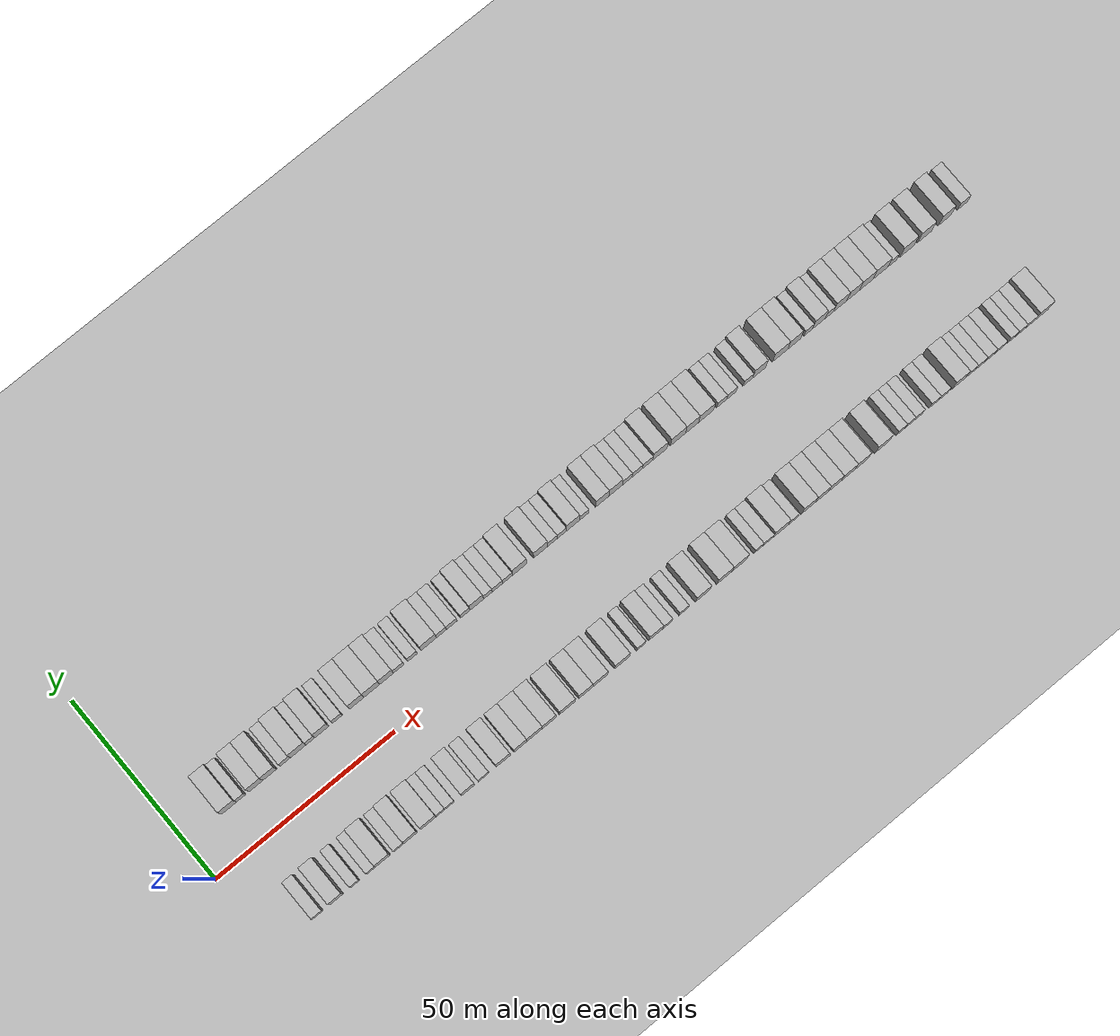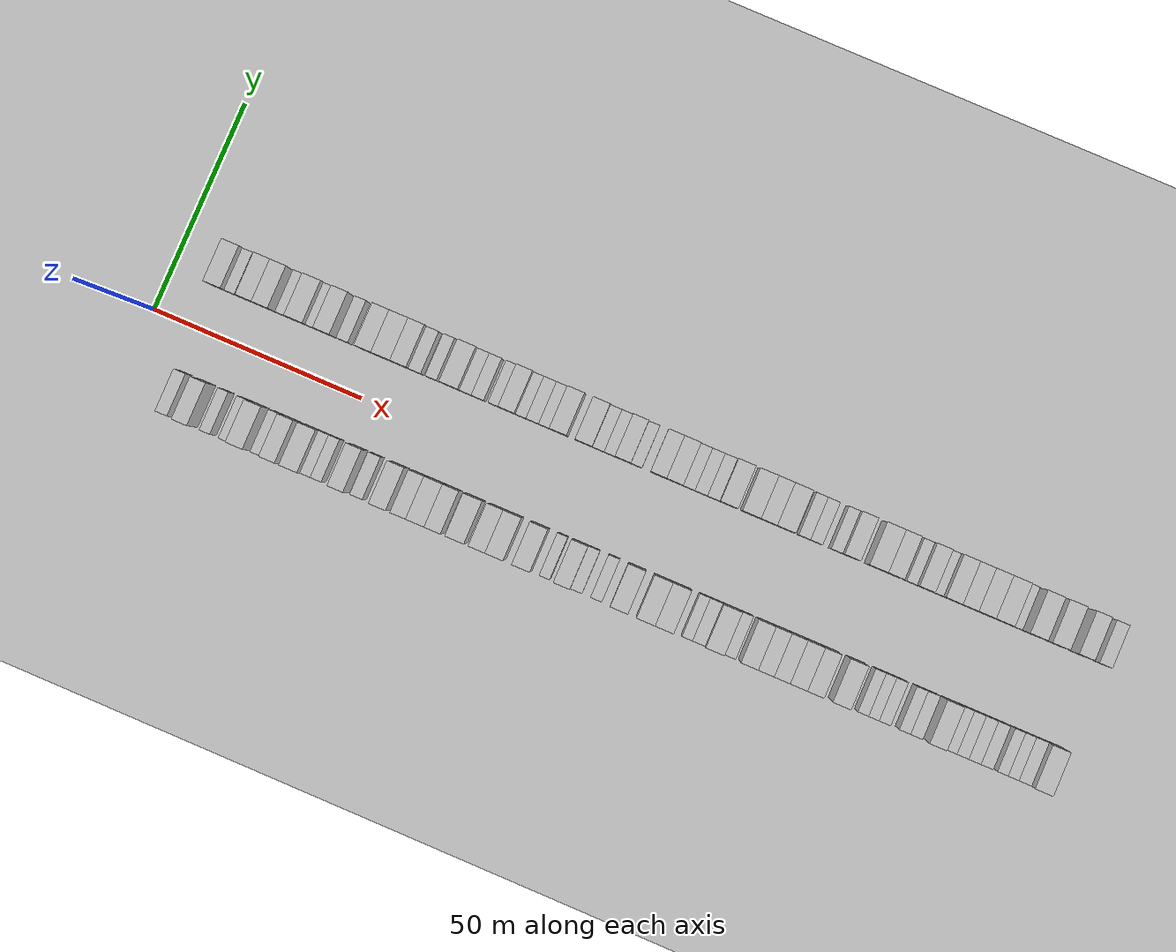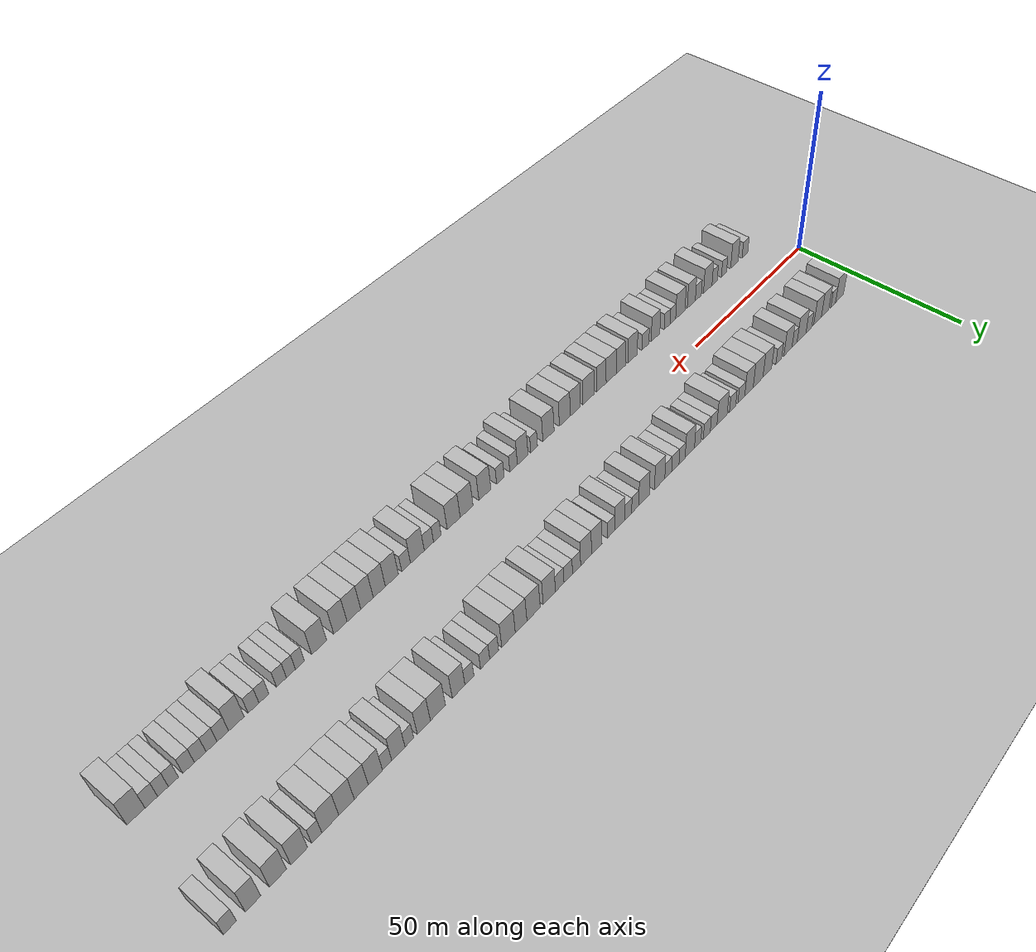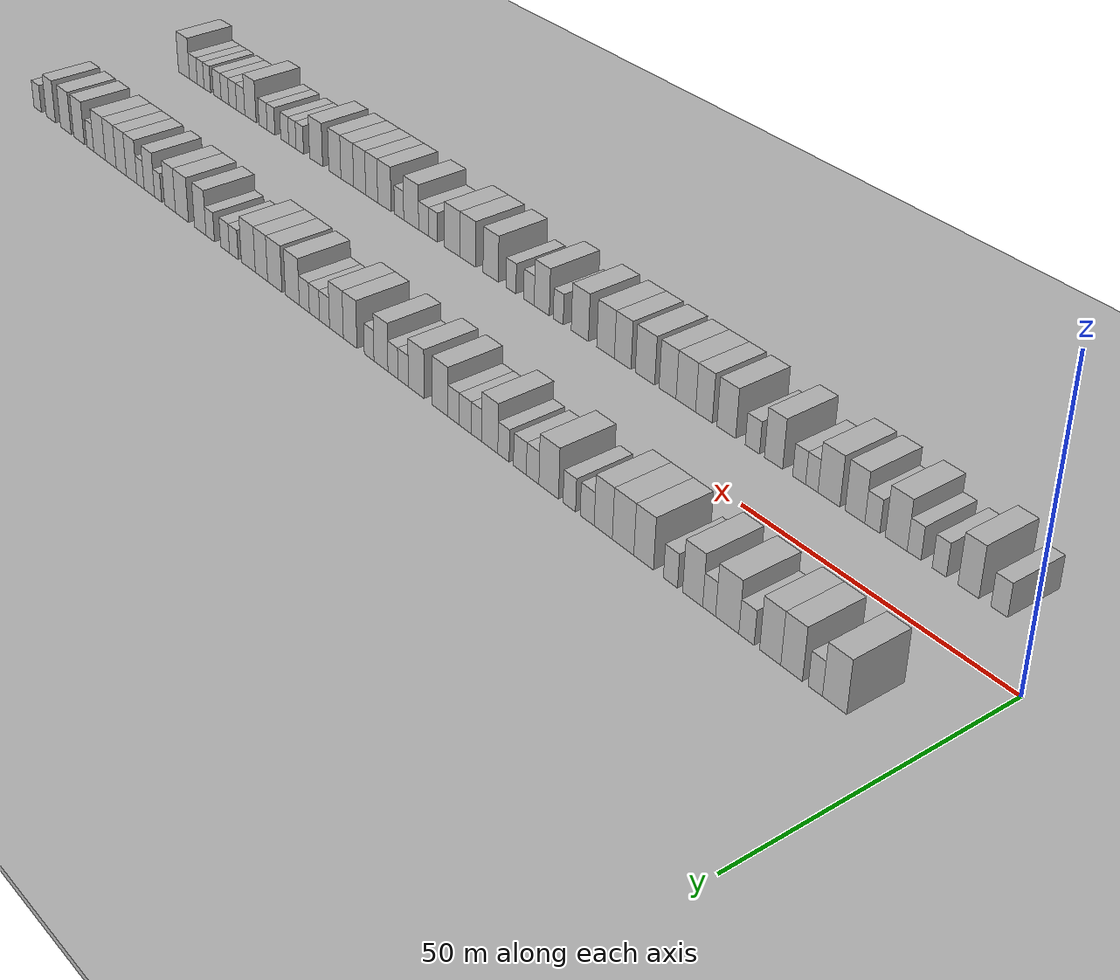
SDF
<?xml version="1.0" encoding="utf-8"?>

<sdf version="1.6">

   <world name="default">

      <gui fullscreen="0">

         <camera name="user_camera">

            <pose>-15 0 4.57585 0 0 0</pose>

            <view_controller>orbit</view_controller>

         </camera>

      </gui>

      <scene>

         <sky>

           <clouds>

             <speed>12</speed>

           </clouds>

         </sky>

         <ambient>0.4 0.4 0.4 1</ambient>

         <background>0.7 0.7 0.7 1</background>

         <shadows>1</shadows>

      </scene>

      <gravity>0 0 -9.8066</gravity>

      <magnetic_field>6e-06 2.3e-05 -4.2e-05</magnetic_field>

      <physics default="0" name="default_physics" type="ode">

         <ode>

            <solver>

               <type>quick</type>

               <iters>10</iters>

               <sor>1.0</sor>

               <use_dynamic_moi_rescaling>0</use_dynamic_moi_rescaling>

            </solver>

            <constraints>

               <cfm>0</cfm>

               <erp>0.2</erp>

               <contact_max_correcting_vel>100</contact_max_correcting_vel>

               <contact_surface_layer>0.001</contact_surface_layer>

            </constraints>

         </ode>

         <max_step_size>0.004</max_step_size>

         <real_time_factor>1</real_time_factor>

         <real_time_update_rate>250</real_time_update_rate>

      </physics>

      <light name="sun" type="directional">

         <cast_shadows>1</cast_shadows>

         <pose>0 0 10 0 0 0</pose>

         <diffuse>0.8 0.8 0.8 1</diffuse>

         <specular>0.2 0.2 0.2 1</specular>

         <attenuation>

            <range>1000</range>

            <constant>0.9</constant>

            <linear>0.01</linear>

            <quadratic>0.001</quadratic>

         </attenuation>

         <direction>-0.5 0.1 -0.9</direction>

      </light>

      <include>

         <name>ground_plane_1</name>

         <uri>model://HANNAS_ground_plane</uri>

         <pose>0 0 0  0 0 0</pose>

      </include>

      <include>

         <name>ground_plane_2</name>

         <uri>model://HANNAS_ground_plane</uri>

         <pose>100 0 0  0 0 0</pose>

      </include>

      <model name="building_1">

         <static>1</static>

         <pose frame="">12.0635 15.0000 0 0.000000 0.000000 1.570796</pose>

         <link name="link">

            <pose frame="">0 0 4.50 0 0 0</pose>

            <collision name="collision">

               <geometry>

                  <box>

                     <size>10.0000 4.1269 9.0000</size>

                  </box>

               </geometry>

               <max_contacts>10</max_contacts>

               <surface>

                  <contact>

                     <ode/>

                  </contact>

                  <bounce/>

                  <friction>

                     <torsional>

                        <ode/>

                     </torsional>

                     <ode/>

                  </friction>

               </surface>

            </collision>

            <visual name="visual">

               <cast_shadows>0</cast_shadows>

               <geometry>

                  <box>

                     <size>10.0000 4.1269 9.0000</size>

                  </box>

               </geometry>

               <material>

                  <script>

                     <uri>model://HANNAS_wall/materials/scripts</uri>

                     <uri>model://HANNAS_wall/materials/textures</uri>

                     <name>vrc/HANNAS_wall</name>

                  </script>

               </material>

            </visual>

            <self_collide>0</self_collide>

            <enable_wind>0</enable_wind>

            <kinematic>0</kinematic>

         </link>

      </model>

      <model name="building_2">

         <static>1</static>

         <pose frame="">15.3622 15.0000 0 0.000000 0.000000 1.570796</pose>

         <link name="link">

            <pose frame="">0 0 3.00 0 0 0</pose>

            <collision name="collision">

               <geometry>

                  <box>

                     <size>10.0000 2.4706 6.0000</size>

                  </box>

               </geometry>

               <max_contacts>10</max_contacts>

               <surface>

                  <contact>

                     <ode/>

                  </contact>

                  <bounce/>

                  <friction>

                     <torsional>

                        <ode/>

                     </torsional>

                     <ode/>

                  </friction>

               </surface>

            </collision>

            <visual name="visual">

               <cast_shadows>0</cast_shadows>

               <geometry>

                  <box>

                     <size>10.0000 2.4706 6.0000</size>

                  </box>

               </geometry>

               <material>

                  <script>

                     <uri>model://HANNAS_wall/materials/scripts</uri>

                     <uri>model://HANNAS_wall/materials/textures</uri>

                     <name>vrc/HANNAS_wall</name>

                  </script>

               </material>

            </visual>

            <self_collide>0</self_collide>

            <enable_wind>0</enable_wind>

            <kinematic>0</kinematic>

         </link>

      </model>

      <model name="building_3">

         <static>1</static>

         <pose frame="">19.5096 15.0000 0 0.000000 0.000000 1.570796</pose>

         <link name="link">

            <pose frame="">0 0 4.50 0 0 0</pose>

            <collision name="collision">

               <geometry>

                  <box>

                     <size>10.0000 3.8242 9.0000</size>

                  </box>

               </geometry>

               <max_contacts>10</max_contacts>

               <surface>

                  <contact>

                     <ode/>

                  </contact>

                  <bounce/>

                  <friction>

                     <torsional>

                        <ode/>

                     </torsional>

                     <ode/>

                  </friction>

               </surface>

            </collision>

            <visual name="visual">

               <cast_shadows>0</cast_shadows>

               <geometry>

                  <box>

                     <size>10.0000 3.8242 9.0000</size>

                  </box>

               </geometry>

               <material>

                  <script>

                     <uri>model://HANNAS_wall/materials/scripts</uri>

                     <uri>model://HANNAS_wall/materials/textures</uri>

                     <name>vrc/HANNAS_wall</name>

                  </script>

               </material>

            </visual>

            <self_collide>0</self_collide>

            <enable_wind>0</enable_wind>

            <kinematic>0</kinematic>

         </link>

      </model>

      <model name="building_4">

         <static>1</static>

         <pose frame="">23.3249 15.0000 0 0.000000 0.000000 1.570796</pose>

         <link name="link">

            <pose frame="">0 0 4.50 0 0 0</pose>

            <collision name="collision">

               <geometry>

                  <box>

                     <size>10.0000 3.8064 9.0000</size>

                  </box>

               </geometry>

               <max_contacts>10</max_contacts>

               <surface>

                  <contact>

                     <ode/>

                  </contact>

                  <bounce/>

                  <friction>

                     <torsional>

                        <ode/>

                     </torsional>

                     <ode/>

                  </friction>

               </surface>

            </collision>

            <visual name="visual">

               <cast_shadows>0</cast_shadows>

               <geometry>

                  <box>

                     <size>10.0000 3.8064 9.0000</size>

                  </box>

               </geometry>

               <material>

                  <script>

                     <uri>model://HANNAS_wall/materials/scripts</uri>

                     <uri>model://HANNAS_wall/materials/textures</uri>

                     <name>vrc/HANNAS_wall</name>

                  </script>

               </material>

            </visual>

            <self_collide>0</self_collide>

            <enable_wind>0</enable_wind>

            <kinematic>0</kinematic>

         </link>

      </model>

      <model name="building_5">

         <static>1</static>

         <pose frame="">27.6384 15.0000 0 0.000000 0.000000 1.570796</pose>

         <link name="link">

            <pose frame="">0 0 3.00 0 0 0</pose>

            <collision name="collision">

               <geometry>

                  <box>

                     <size>10.0000 2.8205 6.0000</size>

                  </box>

               </geometry>

               <max_contacts>10</max_contacts>

               <surface>

                  <contact>

                     <ode/>

                  </contact>

                  <bounce/>

                  <friction>

                     <torsional>

                        <ode/>

                     </torsional>

                     <ode/>

                  </friction>

               </surface>

            </collision>

            <visual name="visual">

               <cast_shadows>0</cast_shadows>

               <geometry>

                  <box>

                     <size>10.0000 2.8205 6.0000</size>

                  </box>

               </geometry>

               <material>

                  <script>

                     <uri>model://HANNAS_wall/materials/scripts</uri>

                     <uri>model://HANNAS_wall/materials/textures</uri>

                     <name>vrc/HANNAS_wall</name>

                  </script>

               </material>

            </visual>

            <self_collide>0</self_collide>

            <enable_wind>0</enable_wind>

            <kinematic>0</kinematic>

         </link>

      </model>

      <model name="building_6">

         <static>1</static>

         <pose frame="">31.2251 15.0000 0 0.000000 0.000000 1.570796</pose>

         <link name="link">

            <pose frame="">0 0 4.50 0 0 0</pose>

            <collision name="collision">

               <geometry>

                  <box>

                     <size>10.0000 4.3530 9.0000</size>

                  </box>

               </geometry>

               <max_contacts>10</max_contacts>

               <surface>

                  <contact>

                     <ode/>

                  </contact>

                  <bounce/>

                  <friction>

                     <torsional>

                        <ode/>

                     </torsional>

                     <ode/>

                  </friction>

               </surface>

            </collision>

            <visual name="visual">

               <cast_shadows>0</cast_shadows>

               <geometry>

                  <box>

                     <size>10.0000 4.3530 9.0000</size>

                  </box>

               </geometry>

               <material>

                  <script>

                     <uri>model://HANNAS_wall/materials/scripts</uri>

                     <uri>model://HANNAS_wall/materials/textures</uri>

                     <name>vrc/HANNAS_wall</name>

                  </script>

               </material>

            </visual>

            <self_collide>0</self_collide>

            <enable_wind>0</enable_wind>

            <kinematic>0</kinematic>

         </link>

      </model>

      <model name="building_7">

         <static>1</static>

         <pose frame="">34.6320 15.0000 0 0.000000 0.000000 1.570796</pose>

         <link name="link">

            <pose frame="">0 0 3.00 0 0 0</pose>

            <collision name="collision">

               <geometry>

                  <box>

                     <size>10.0000 2.4608 6.0000</size>

                  </box>

               </geometry>

               <max_contacts>10</max_contacts>

               <surface>

                  <contact>

                     <ode/>

                  </contact>

                  <bounce/>

                  <friction>

                     <torsional>

                        <ode/>

                     </torsional>

                     <ode/>

                  </friction>

               </surface>

            </collision>

            <visual name="visual">

               <cast_shadows>0</cast_shadows>

               <geometry>

                  <box>

                     <size>10.0000 2.4608 6.0000</size>

                  </box>

               </geometry>

               <material>

                  <script>

                     <uri>model://HANNAS_wall/materials/scripts</uri>

                     <uri>model://HANNAS_wall/materials/textures</uri>

                     <name>vrc/HANNAS_wall</name>

                  </script>

               </material>

            </visual>

            <self_collide>0</self_collide>

            <enable_wind>0</enable_wind>

            <kinematic>0</kinematic>

         </link>

      </model>

      <model name="building_8">

         <static>1</static>

         <pose frame="">37.8067 15.0000 0 0.000000 0.000000 1.570796</pose>

         <link name="link">

            <pose frame="">0 0 4.50 0 0 0</pose>

            <collision name="collision">

               <geometry>

                  <box>

                     <size>10.0000 3.8886 9.0000</size>

                  </box>

               </geometry>

               <max_contacts>10</max_contacts>

               <surface>

                  <contact>

                     <ode/>

                  </contact>

                  <bounce/>

                  <friction>

                     <torsional>

                        <ode/>

                     </torsional>

                     <ode/>

                  </friction>

               </surface>

            </collision>

            <visual name="visual">

               <cast_shadows>0</cast_shadows>

               <geometry>

                  <box>

                     <size>10.0000 3.8886 9.0000</size>

                  </box>

               </geometry>

               <material>

                  <script>

                     <uri>model://HANNAS_wall/materials/scripts</uri>

                     <uri>model://HANNAS_wall/materials/textures</uri>

                     <name>vrc/HANNAS_wall</name>

                  </script>

               </material>

            </visual>

            <self_collide>0</self_collide>

            <enable_wind>0</enable_wind>

            <kinematic>0</kinematic>

         </link>

      </model>

      <model name="building_9">

         <static>1</static>

         <pose frame="">42.1384 15.0000 0 0.000000 0.000000 1.570796</pose>

         <link name="link">

            <pose frame="">0 0 3.00 0 0 0</pose>

            <collision name="collision">

               <geometry>

                  <box>

                     <size>10.0000 2.7749 6.0000</size>

                  </box>

               </geometry>

               <max_contacts>10</max_contacts>

               <surface>

                  <contact>

                     <ode/>

                  </contact>

                  <bounce/>

                  <friction>

                     <torsional>

                        <ode/>

                     </torsional>

                     <ode/>

                  </friction>

               </surface>

            </collision>

            <visual name="visual">

               <cast_shadows>0</cast_shadows>

               <geometry>

                  <box>

                     <size>10.0000 2.7749 6.0000</size>

                  </box>

               </geometry>

               <material>

                  <script>

                     <uri>model://HANNAS_wall/materials/scripts</uri>

                     <uri>model://HANNAS_wall/materials/textures</uri>

                     <name>vrc/HANNAS_wall</name>

                  </script>

               </material>

            </visual>

            <self_collide>0</self_collide>

            <enable_wind>0</enable_wind>

            <kinematic>0</kinematic>

         </link>

      </model>

      <model name="building_10">

         <static>1</static>

         <pose frame="">47.5163 15.0000 0 0.000000 0.000000 1.570796</pose>

         <link name="link">

            <pose frame="">0 0 4.50 0 0 0</pose>

            <collision name="collision">

               <geometry>

                  <box>

                     <size>10.0000 3.9808 9.0000</size>

                  </box>

               </geometry>

               <max_contacts>10</max_contacts>

               <surface>

                  <contact>

                     <ode/>

                  </contact>

                  <bounce/>

                  <friction>

                     <torsional>

                        <ode/>

                     </torsional>

                     <ode/>

                  </friction>

               </surface>

            </collision>

            <visual name="visual">

               <cast_shadows>0</cast_shadows>

               <geometry>

                  <box>

                     <size>10.0000 3.9808 9.0000</size>

                  </box>

               </geometry>

               <material>

                  <script>

                     <uri>model://HANNAS_wall/materials/scripts</uri>

                     <uri>model://HANNAS_wall/materials/textures</uri>

                     <name>vrc/HANNAS_wall</name>

                  </script>

               </material>

            </visual>

            <self_collide>0</self_collide>

            <enable_wind>0</enable_wind>

            <kinematic>0</kinematic>

         </link>

      </model>

      <model name="building_11">

         <static>1</static>

         <pose frame="">51.7350 15.0000 0 0.000000 0.000000 1.570796</pose>

         <link name="link">

            <pose frame="">0 0 4.50 0 0 0</pose>

            <collision name="collision">

               <geometry>

                  <box>

                     <size>10.0000 4.4566 9.0000</size>

                  </box>

               </geometry>

               <max_contacts>10</max_contacts>

               <surface>

                  <contact>

                     <ode/>

                  </contact>

                  <bounce/>

                  <friction>

                     <torsional>

                        <ode/>

                     </torsional>

                     <ode/>

                  </friction>

               </surface>

            </collision>

            <visual name="visual">

               <cast_shadows>0</cast_shadows>

               <geometry>

                  <box>

                     <size>10.0000 4.4566 9.0000</size>

                  </box>

               </geometry>

               <material>

                  <script>

                     <uri>model://HANNAS_wall/materials/scripts</uri>

                     <uri>model://HANNAS_wall/materials/textures</uri>

                     <name>vrc/HANNAS_wall</name>

                  </script>

               </material>

            </visual>

            <self_collide>0</self_collide>

            <enable_wind>0</enable_wind>

            <kinematic>0</kinematic>

         </link>

      </model>

      <model name="building_12">

         <static>1</static>

         <pose frame="">55.8778 15.0000 0 0.000000 0.000000 1.570796</pose>

         <link name="link">

            <pose frame="">0 0 4.50 0 0 0</pose>

            <collision name="collision">

               <geometry>

                  <box>

                     <size>10.0000 3.8290 9.0000</size>

                  </box>

               </geometry>

               <max_contacts>10</max_contacts>

               <surface>

                  <contact>

                     <ode/>

                  </contact>

                  <bounce/>

                  <friction>

                     <torsional>

                        <ode/>

                     </torsional>

                     <ode/>

                  </friction>

               </surface>

            </collision>

            <visual name="visual">

               <cast_shadows>0</cast_shadows>

               <geometry>

                  <box>

                     <size>10.0000 3.8290 9.0000</size>

                  </box>

               </geometry>

               <material>

                  <script>

                     <uri>model://HANNAS_wall/materials/scripts</uri>

                     <uri>model://HANNAS_wall/materials/textures</uri>

                     <name>vrc/HANNAS_wall</name>

                  </script>

               </material>

            </visual>

            <self_collide>0</self_collide>

            <enable_wind>0</enable_wind>

            <kinematic>0</kinematic>

         </link>

      </model>

      <model name="building_13">

         <static>1</static>

         <pose frame="">59.2881 15.0000 0 0.000000 0.000000 1.570796</pose>

         <link name="link">

            <pose frame="">0 0 3.00 0 0 0</pose>

            <collision name="collision">

               <geometry>

                  <box>

                     <size>10.0000 2.9917 6.0000</size>

                  </box>

               </geometry>

               <max_contacts>10</max_contacts>

               <surface>

                  <contact>

                     <ode/>

                  </contact>

                  <bounce/>

                  <friction>

                     <torsional>

                        <ode/>

                     </torsional>

                     <ode/>

                  </friction>

               </surface>

            </collision>

            <visual name="visual">

               <cast_shadows>0</cast_shadows>

               <geometry>

                  <box>

                     <size>10.0000 2.9917 6.0000</size>

                  </box>

               </geometry>

               <material>

                  <script>

                     <uri>model://HANNAS_wall/materials/scripts</uri>

                     <uri>model://HANNAS_wall/materials/textures</uri>

                     <name>vrc/HANNAS_wall</name>

                  </script>

               </material>

            </visual>

            <self_collide>0</self_collide>

            <enable_wind>0</enable_wind>

            <kinematic>0</kinematic>

         </link>

      </model>

      <model name="building_14">

         <static>1</static>

         <pose frame="">63.1467 15.0000 0 0.000000 0.000000 1.570796</pose>

         <link name="link">

            <pose frame="">0 0 3.00 0 0 0</pose>

            <collision name="collision">

               <geometry>

                  <box>

                     <size>10.0000 2.7255 6.0000</size>

                  </box>

               </geometry>

               <max_contacts>10</max_contacts>

               <surface>

                  <contact>

                     <ode/>

                  </contact>

                  <bounce/>

                  <friction>

                     <torsional>

                        <ode/>

                     </torsional>

                     <ode/>

                  </friction>

               </surface>

            </collision>

            <visual name="visual">

               <cast_shadows>0</cast_shadows>

               <geometry>

                  <box>

                     <size>10.0000 2.7255 6.0000</size>

                  </box>

               </geometry>

               <material>

                  <script>

                     <uri>model://HANNAS_wall/materials/scripts</uri>

                     <uri>model://HANNAS_wall/materials/textures</uri>

                     <name>vrc/HANNAS_wall</name>

                  </script>

               </material>

            </visual>

            <self_collide>0</self_collide>

            <enable_wind>0</enable_wind>

            <kinematic>0</kinematic>

         </link>

      </model>

      <model name="building_15">

         <static>1</static>

         <pose frame="">67.6965 15.0000 0 0.000000 0.000000 1.570796</pose>

         <link name="link">

            <pose frame="">0 0 4.50 0 0 0</pose>

            <collision name="collision">

               <geometry>

                  <box>

                     <size>10.0000 4.3741 9.0000</size>

                  </box>

               </geometry>

               <max_contacts>10</max_contacts>

               <surface>

                  <contact>

                     <ode/>

                  </contact>

                  <bounce/>

                  <friction>

                     <torsional>

                        <ode/>

                     </torsional>

                     <ode/>

                  </friction>

               </surface>

            </collision>

            <visual name="visual">

               <cast_shadows>0</cast_shadows>

               <geometry>

                  <box>

                     <size>10.0000 4.3741 9.0000</size>

                  </box>

               </geometry>

               <material>

                  <script>

                     <uri>model://HANNAS_wall/materials/scripts</uri>

                     <uri>model://HANNAS_wall/materials/textures</uri>

                     <name>vrc/HANNAS_wall</name>

                  </script>

               </material>

            </visual>

            <self_collide>0</self_collide>

            <enable_wind>0</enable_wind>

            <kinematic>0</kinematic>

         </link>

      </model>

      <model name="building_16">

         <static>1</static>

         <pose frame="">71.3023 15.0000 0 0.000000 0.000000 1.570796</pose>

         <link name="link">

            <pose frame="">0 0 3.00 0 0 0</pose>

            <collision name="collision">

               <geometry>

                  <box>

                     <size>10.0000 2.8375 6.0000</size>

                  </box>

               </geometry>

               <max_contacts>10</max_contacts>

               <surface>

                  <contact>

                     <ode/>

                  </contact>

                  <bounce/>

                  <friction>

                     <torsional>

                        <ode/>

                     </torsional>

                     <ode/>

                  </friction>

               </surface>

            </collision>

            <visual name="visual">

               <cast_shadows>0</cast_shadows>

               <geometry>

                  <box>

                     <size>10.0000 2.8375 6.0000</size>

                  </box>

               </geometry>

               <material>

                  <script>

                     <uri>model://HANNAS_wall/materials/scripts</uri>

                     <uri>model://HANNAS_wall/materials/textures</uri>

                     <name>vrc/HANNAS_wall</name>

                  </script>

               </material>

            </visual>

            <self_collide>0</self_collide>

            <enable_wind>0</enable_wind>

            <kinematic>0</kinematic>

         </link>

      </model>

      <model name="building_17">

         <static>1</static>

         <pose frame="">74.1997 15.0000 0 0.000000 0.000000 1.570796</pose>

         <link name="link">

            <pose frame="">0 0 3.00 0 0 0</pose>

            <collision name="collision">

               <geometry>

                  <box>

                     <size>10.0000 2.9573 6.0000</size>

                  </box>

               </geometry>

               <max_contacts>10</max_contacts>

               <surface>

                  <contact>

                     <ode/>

                  </contact>

                  <bounce/>

                  <friction>

                     <torsional>

                        <ode/>

                     </torsional>

                     <ode/>

                  </friction>

               </surface>

            </collision>

            <visual name="visual">

               <cast_shadows>0</cast_shadows>

               <geometry>

                  <box>

                     <size>10.0000 2.9573 6.0000</size>

                  </box>

               </geometry>

               <material>

                  <script>

                     <uri>model://HANNAS_wall/materials/scripts</uri>

                     <uri>model://HANNAS_wall/materials/textures</uri>

                     <name>vrc/HANNAS_wall</name>

                  </script>

               </material>

            </visual>

            <self_collide>0</self_collide>

            <enable_wind>0</enable_wind>

            <kinematic>0</kinematic>

         </link>

      </model>

      <model name="building_18">

         <static>1</static>

         <pose frame="">78.0015 15.0000 0 0.000000 0.000000 1.570796</pose>

         <link name="link">

            <pose frame="">0 0 3.00 0 0 0</pose>

            <collision name="collision">

               <geometry>

                  <box>

                     <size>10.0000 2.6463 6.0000</size>

                  </box>

               </geometry>

               <max_contacts>10</max_contacts>

               <surface>

                  <contact>

                     <ode/>

                  </contact>

                  <bounce/>

                  <friction>

                     <torsional>

                        <ode/>

                     </torsional>

                     <ode/>

                  </friction>

               </surface>

            </collision>

            <visual name="visual">

               <cast_shadows>0</cast_shadows>

               <geometry>

                  <box>

                     <size>10.0000 2.6463 6.0000</size>

                  </box>

               </geometry>

               <material>

                  <script>

                     <uri>model://HANNAS_wall/materials/scripts</uri>

                     <uri>model://HANNAS_wall/materials/textures</uri>

                     <name>vrc/HANNAS_wall</name>

                  </script>

               </material>

            </visual>

            <self_collide>0</self_collide>

            <enable_wind>0</enable_wind>

            <kinematic>0</kinematic>

         </link>

      </model>

      <model name="building_19">

         <static>1</static>

         <pose frame="">81.2366 15.0000 0 0.000000 0.000000 1.570796</pose>

         <link name="link">

            <pose frame="">0 0 4.50 0 0 0</pose>

            <collision name="collision">

               <geometry>

                  <box>

                     <size>10.0000 3.8238 9.0000</size>

                  </box>

               </geometry>

               <max_contacts>10</max_contacts>

               <surface>

                  <contact>

                     <ode/>

                  </contact>

                  <bounce/>

                  <friction>

                     <torsional>

                        <ode/>

                     </torsional>

                     <ode/>

                  </friction>

               </surface>

            </collision>

            <visual name="visual">

               <cast_shadows>0</cast_shadows>

               <geometry>

                  <box>

                     <size>10.0000 3.8238 9.0000</size>

                  </box>

               </geometry>

               <material>

                  <script>

                     <uri>model://HANNAS_wall/materials/scripts</uri>

                     <uri>model://HANNAS_wall/materials/textures</uri>

                     <name>vrc/HANNAS_wall</name>

                  </script>

               </material>

            </visual>

            <self_collide>0</self_collide>

            <enable_wind>0</enable_wind>

            <kinematic>0</kinematic>

         </link>

      </model>

      <model name="building_20">

         <static>1</static>

         <pose frame="">84.3906 15.0000 0 0.000000 0.000000 1.570796</pose>

         <link name="link">

            <pose frame="">0 0 3.00 0 0 0</pose>

            <collision name="collision">

               <geometry>

                  <box>

                     <size>10.0000 2.4841 6.0000</size>

                  </box>

               </geometry>

               <max_contacts>10</max_contacts>

               <surface>

                  <contact>

                     <ode/>

                  </contact>

                  <bounce/>

                  <friction>

                     <torsional>

                        <ode/>

                     </torsional>

                     <ode/>

                  </friction>

               </surface>

            </collision>

            <visual name="visual">

               <cast_shadows>0</cast_shadows>

               <geometry>

                  <box>

                     <size>10.0000 2.4841 6.0000</size>

                  </box>

               </geometry>

               <material>

                  <script>

                     <uri>model://HANNAS_wall/materials/scripts</uri>

                     <uri>model://HANNAS_wall/materials/textures</uri>

                     <name>vrc/HANNAS_wall</name>

                  </script>

               </material>

            </visual>

            <self_collide>0</self_collide>

            <enable_wind>0</enable_wind>

            <kinematic>0</kinematic>

         </link>

      </model>

      <model name="building_21">

         <static>1</static>

         <pose frame="">87.1256 15.0000 0 0.000000 0.000000 1.570796</pose>

         <link name="link">

            <pose frame="">0 0 3.00 0 0 0</pose>

            <collision name="collision">

               <geometry>

                  <box>

                     <size>10.0000 2.9860 6.0000</size>

                  </box>

               </geometry>

               <max_contacts>10</max_contacts>

               <surface>

                  <contact>

                     <ode/>

                  </contact>

                  <bounce/>

                  <friction>

                     <torsional>

                        <ode/>

                     </torsional>

                     <ode/>

                  </friction>

               </surface>

            </collision>

            <visual name="visual">

               <cast_shadows>0</cast_shadows>

               <geometry>

                  <box>

                     <size>10.0000 2.9860 6.0000</size>

                  </box>

               </geometry>

               <material>

                  <script>

                     <uri>model://HANNAS_wall/materials/scripts</uri>

                     <uri>model://HANNAS_wall/materials/textures</uri>

                     <name>vrc/HANNAS_wall</name>

                  </script>

               </material>

            </visual>

            <self_collide>0</self_collide>

            <enable_wind>0</enable_wind>

            <kinematic>0</kinematic>

         </link>

      </model>

      <model name="building_22">

         <static>1</static>

         <pose frame="">89.9670 15.0000 0 0.000000 0.000000 1.570796</pose>

         <link name="link">

            <pose frame="">0 0 3.00 0 0 0</pose>

            <collision name="collision">

               <geometry>

                  <box>

                     <size>10.0000 2.6968 6.0000</size>

                  </box>

               </geometry>

               <max_contacts>10</max_contacts>

               <surface>

                  <contact>

                     <ode/>

                  </contact>

                  <bounce/>

                  <friction>

                     <torsional>

                        <ode/>

                     </torsional>

                     <ode/>

                  </friction>

               </surface>

            </collision>

            <visual name="visual">

               <cast_shadows>0</cast_shadows>

               <geometry>

                  <box>

                     <size>10.0000 2.6968 6.0000</size>

                  </box>

               </geometry>

               <material>

                  <script>

                     <uri>model://HANNAS_wall/materials/scripts</uri>

                     <uri>model://HANNAS_wall/materials/textures</uri>

                     <name>vrc/HANNAS_wall</name>

                  </script>

               </material>

            </visual>

            <self_collide>0</self_collide>

            <enable_wind>0</enable_wind>

            <kinematic>0</kinematic>

         </link>

      </model>

      <model name="building_23">

         <static>1</static>

         <pose frame="">93.3270 15.0000 0 0.000000 0.000000 1.570796</pose>

         <link name="link">

            <pose frame="">0 0 4.50 0 0 0</pose>

            <collision name="collision">

               <geometry>

                  <box>

                     <size>10.0000 4.0232 9.0000</size>

                  </box>

               </geometry>

               <max_contacts>10</max_contacts>

               <surface>

                  <contact>

                     <ode/>

                  </contact>

                  <bounce/>

                  <friction>

                     <torsional>

                        <ode/>

                     </torsional>

                     <ode/>

                  </friction>

               </surface>

            </collision>

            <visual name="visual">

               <cast_shadows>0</cast_shadows>

               <geometry>

                  <box>

                     <size>10.0000 4.0232 9.0000</size>

                  </box>

               </geometry>

               <material>

                  <script>

                     <uri>model://HANNAS_wall/materials/scripts</uri>

                     <uri>model://HANNAS_wall/materials/textures</uri>

                     <name>vrc/HANNAS_wall</name>

                  </script>

               </material>

            </visual>

            <self_collide>0</self_collide>

            <enable_wind>0</enable_wind>

            <kinematic>0</kinematic>

         </link>

      </model>

      <model name="building_24">

         <static>1</static>

         <pose frame="">99.3500 15.0000 0 0.000000 0.000000 1.570796</pose>

         <link name="link">

            <pose frame="">0 0 4.50 0 0 0</pose>

            <collision name="collision">

               <geometry>

                  <box>

                     <size>10.0000 4.0227 9.0000</size>

                  </box>

               </geometry>

               <max_contacts>10</max_contacts>

               <surface>

                  <contact>

                     <ode/>

                  </contact>

                  <bounce/>

                  <friction>

                     <torsional>

                        <ode/>

                     </torsional>

                     <ode/>

                  </friction>

               </surface>

            </collision>

            <visual name="visual">

               <cast_shadows>0</cast_shadows>

               <geometry>

                  <box>

                     <size>10.0000 4.0227 9.0000</size>

                  </box>

               </geometry>

               <material>

                  <script>

                     <uri>model://HANNAS_wall/materials/scripts</uri>

                     <uri>model://HANNAS_wall/materials/textures</uri>

                     <name>vrc/HANNAS_wall</name>

                  </script>

               </material>

            </visual>

            <self_collide>0</self_collide>

            <enable_wind>0</enable_wind>

            <kinematic>0</kinematic>

         </link>

      </model>

      <model name="building_25">

         <static>1</static>

         <pose frame="">102.7177 15.0000 0 0.000000 0.000000 1.570796</pose>

         <link name="link">

            <pose frame="">0 0 3.00 0 0 0</pose>

            <collision name="collision">

               <geometry>

                  <box>

                     <size>10.0000 2.7128 6.0000</size>

                  </box>

               </geometry>

               <max_contacts>10</max_contacts>

               <surface>

                  <contact>

                     <ode/>

                  </contact>

                  <bounce/>

                  <friction>

                     <torsional>

                        <ode/>

                     </torsional>

                     <ode/>

                  </friction>

               </surface>

            </collision>

            <visual name="visual">

               <cast_shadows>0</cast_shadows>

               <geometry>

                  <box>

                     <size>10.0000 2.7128 6.0000</size>

                  </box>

               </geometry>

               <material>

                  <script>

                     <uri>model://HANNAS_wall/materials/scripts</uri>

                     <uri>model://HANNAS_wall/materials/textures</uri>

                     <name>vrc/HANNAS_wall</name>

                  </script>

               </material>

            </visual>

            <self_collide>0</self_collide>

            <enable_wind>0</enable_wind>

            <kinematic>0</kinematic>

         </link>

      </model>

      <model name="building_26">

         <static>1</static>

         <pose frame="">105.3841 15.0000 0 0.000000 0.000000 1.570796</pose>

         <link name="link">

            <pose frame="">0 0 3.00 0 0 0</pose>

            <collision name="collision">

               <geometry>

                  <box>

                     <size>10.0000 2.6202 6.0000</size>

                  </box>

               </geometry>

               <max_contacts>10</max_contacts>

               <surface>

                  <contact>

                     <ode/>

                  </contact>

                  <bounce/>

                  <friction>

                     <torsional>

                        <ode/>

                     </torsional>

                     <ode/>

                  </friction>

               </surface>

            </collision>

            <visual name="visual">

               <cast_shadows>0</cast_shadows>

               <geometry>

                  <box>

                     <size>10.0000 2.6202 6.0000</size>

                  </box>

               </geometry>

               <material>

                  <script>

                     <uri>model://HANNAS_wall/materials/scripts</uri>

                     <uri>model://HANNAS_wall/materials/textures</uri>

                     <name>vrc/HANNAS_wall</name>

                  </script>

               </material>

            </visual>

            <self_collide>0</self_collide>

            <enable_wind>0</enable_wind>

            <kinematic>0</kinematic>

         </link>

      </model>

      <model name="building_27">

         <static>1</static>

         <pose frame="">108.5547 15.0000 0 0.000000 0.000000 1.570796</pose>

         <link name="link">

            <pose frame="">0 0 4.50 0 0 0</pose>

            <collision name="collision">

               <geometry>

                  <box>

                     <size>10.0000 3.7210 9.0000</size>

                  </box>

               </geometry>

               <max_contacts>10</max_contacts>

               <surface>

                  <contact>

                     <ode/>

                  </contact>

                  <bounce/>

                  <friction>

                     <torsional>

                        <ode/>

                     </torsional>

                     <ode/>

                  </friction>

               </surface>

            </collision>

            <visual name="visual">

               <cast_shadows>0</cast_shadows>

               <geometry>

                  <box>

                     <size>10.0000 3.7210 9.0000</size>

                  </box>

               </geometry>

               <material>

                  <script>

                     <uri>model://HANNAS_wall/materials/scripts</uri>

                     <uri>model://HANNAS_wall/materials/textures</uri>

                     <name>vrc/HANNAS_wall</name>

                  </script>

               </material>

            </visual>

            <self_collide>0</self_collide>

            <enable_wind>0</enable_wind>

            <kinematic>0</kinematic>

         </link>

      </model>

      <model name="building_28">

         <static>1</static>

         <pose frame="">111.7187 15.0000 0 0.000000 0.000000 1.570796</pose>

         <link name="link">

            <pose frame="">0 0 3.00 0 0 0</pose>

            <collision name="collision">

               <geometry>

                  <box>

                     <size>10.0000 2.6071 6.0000</size>

                  </box>

               </geometry>

               <max_contacts>10</max_contacts>

               <surface>

                  <contact>

                     <ode/>

                  </contact>

                  <bounce/>

                  <friction>

                     <torsional>

                        <ode/>

                     </torsional>

                     <ode/>

                  </friction>

               </surface>

            </collision>

            <visual name="visual">

               <cast_shadows>0</cast_shadows>

               <geometry>

                  <box>

                     <size>10.0000 2.6071 6.0000</size>

                  </box>

               </geometry>

               <material>

                  <script>

                     <uri>model://HANNAS_wall/materials/scripts</uri>

                     <uri>model://HANNAS_wall/materials/textures</uri>

                     <name>vrc/HANNAS_wall</name>

                  </script>

               </material>

            </visual>

            <self_collide>0</self_collide>

            <enable_wind>0</enable_wind>

            <kinematic>0</kinematic>

         </link>

      </model>

      <model name="building_29">

         <static>1</static>

         <pose frame="">116.8964 15.0000 0 0.000000 0.000000 1.570796</pose>

         <link name="link">

            <pose frame="">0 0 4.50 0 0 0</pose>

            <collision name="collision">

               <geometry>

                  <box>

                     <size>10.0000 3.7483 9.0000</size>

                  </box>

               </geometry>

               <max_contacts>10</max_contacts>

               <surface>

                  <contact>

                     <ode/>

                  </contact>

                  <bounce/>

                  <friction>

                     <torsional>

                        <ode/>

                     </torsional>

                     <ode/>

                  </friction>

               </surface>

            </collision>

            <visual name="visual">

               <cast_shadows>0</cast_shadows>

               <geometry>

                  <box>

                     <size>10.0000 3.7483 9.0000</size>

                  </box>

               </geometry>

               <material>

                  <script>

                     <uri>model://HANNAS_wall/materials/scripts</uri>

                     <uri>model://HANNAS_wall/materials/textures</uri>

                     <name>vrc/HANNAS_wall</name>

                  </script>

               </material>

            </visual>

            <self_collide>0</self_collide>

            <enable_wind>0</enable_wind>

            <kinematic>0</kinematic>

         </link>

      </model>

      <model name="building_30">

         <static>1</static>

         <pose frame="">120.6989 15.0000 0 0.000000 0.000000 1.570796</pose>

         <link name="link">

            <pose frame="">0 0 4.50 0 0 0</pose>

            <collision name="collision">

               <geometry>

                  <box>

                     <size>10.0000 3.8567 9.0000</size>

                  </box>

               </geometry>

               <max_contacts>10</max_contacts>

               <surface>

                  <contact>

                     <ode/>

                  </contact>

                  <bounce/>

                  <friction>

                     <torsional>

                        <ode/>

                     </torsional>

                     <ode/>

                  </friction>

               </surface>

            </collision>

            <visual name="visual">

               <cast_shadows>0</cast_shadows>

               <geometry>

                  <box>

                     <size>10.0000 3.8567 9.0000</size>

                  </box>

               </geometry>

               <material>

                  <script>

                     <uri>model://HANNAS_wall/materials/scripts</uri>

                     <uri>model://HANNAS_wall/materials/textures</uri>

                     <name>vrc/HANNAS_wall</name>

                  </script>

               </material>

            </visual>

            <self_collide>0</self_collide>

            <enable_wind>0</enable_wind>

            <kinematic>0</kinematic>

         </link>

      </model>

      <model name="building_31">

         <static>1</static>

         <pose frame="">124.0344 15.0000 0 0.000000 0.000000 1.570796</pose>

         <link name="link">

            <pose frame="">0 0 3.00 0 0 0</pose>

            <collision name="collision">

               <geometry>

                  <box>

                     <size>10.0000 2.8143 6.0000</size>

                  </box>

               </geometry>

               <max_contacts>10</max_contacts>

               <surface>

                  <contact>

                     <ode/>

                  </contact>

                  <bounce/>

                  <friction>

                     <torsional>

                        <ode/>

                     </torsional>

                     <ode/>

                  </friction>

               </surface>

            </collision>

            <visual name="visual">

               <cast_shadows>0</cast_shadows>

               <geometry>

                  <box>

                     <size>10.0000 2.8143 6.0000</size>

                  </box>

               </geometry>

               <material>

                  <script>

                     <uri>model://HANNAS_wall/materials/scripts</uri>

                     <uri>model://HANNAS_wall/materials/textures</uri>

                     <name>vrc/HANNAS_wall</name>

                  </script>

               </material>

            </visual>

            <self_collide>0</self_collide>

            <enable_wind>0</enable_wind>

            <kinematic>0</kinematic>

         </link>

      </model>

      <model name="building_32">

         <static>1</static>

         <pose frame="">126.9195 15.0000 0 0.000000 0.000000 1.570796</pose>

         <link name="link">

            <pose frame="">0 0 3.00 0 0 0</pose>

            <collision name="collision">

               <geometry>

                  <box>

                     <size>10.0000 2.9560 6.0000</size>

                  </box>

               </geometry>

               <max_contacts>10</max_contacts>

               <surface>

                  <contact>

                     <ode/>

                  </contact>

                  <bounce/>

                  <friction>

                     <torsional>

                        <ode/>

                     </torsional>

                     <ode/>

                  </friction>

               </surface>

            </collision>

            <visual name="visual">

               <cast_shadows>0</cast_shadows>

               <geometry>

                  <box>

                     <size>10.0000 2.9560 6.0000</size>

                  </box>

               </geometry>

               <material>

                  <script>

                     <uri>model://HANNAS_wall/materials/scripts</uri>

                     <uri>model://HANNAS_wall/materials/textures</uri>

                     <name>vrc/HANNAS_wall</name>

                  </script>

               </material>

            </visual>

            <self_collide>0</self_collide>

            <enable_wind>0</enable_wind>

            <kinematic>0</kinematic>

         </link>

      </model>

      <model name="building_33">

         <static>1</static>

         <pose frame="">129.8543 15.0000 0 0.000000 0.000000 1.570796</pose>

         <link name="link">

            <pose frame="">0 0 3.00 0 0 0</pose>

            <collision name="collision">

               <geometry>

                  <box>

                     <size>10.0000 2.9135 6.0000</size>

                  </box>

               </geometry>

               <max_contacts>10</max_contacts>

               <surface>

                  <contact>

                     <ode/>

                  </contact>

                  <bounce/>

                  <friction>

                     <torsional>

                        <ode/>

                     </torsional>

                     <ode/>

                  </friction>

               </surface>

            </collision>

            <visual name="visual">

               <cast_shadows>0</cast_shadows>

               <geometry>

                  <box>

                     <size>10.0000 2.9135 6.0000</size>

                  </box>

               </geometry>

               <material>

                  <script>

                     <uri>model://HANNAS_wall/materials/scripts</uri>

                     <uri>model://HANNAS_wall/materials/textures</uri>

                     <name>vrc/HANNAS_wall</name>

                  </script>

               </material>

            </visual>

            <self_collide>0</self_collide>

            <enable_wind>0</enable_wind>

            <kinematic>0</kinematic>

         </link>

      </model>

      <model name="building_34">

         <static>1</static>

         <pose frame="">133.3670 15.0000 0 0.000000 0.000000 1.570796</pose>

         <link name="link">

            <pose frame="">0 0 4.50 0 0 0</pose>

            <collision name="collision">

               <geometry>

                  <box>

                     <size>10.0000 4.1120 9.0000</size>

                  </box>

               </geometry>

               <max_contacts>10</max_contacts>

               <surface>

                  <contact>

                     <ode/>

                  </contact>

                  <bounce/>

                  <friction>

                     <torsional>

                        <ode/>

                     </torsional>

                     <ode/>

                  </friction>

               </surface>

            </collision>

            <visual name="visual">

               <cast_shadows>0</cast_shadows>

               <geometry>

                  <box>

                     <size>10.0000 4.1120 9.0000</size>

                  </box>

               </geometry>

               <material>

                  <script>

                     <uri>model://HANNAS_wall/materials/scripts</uri>

                     <uri>model://HANNAS_wall/materials/textures</uri>

                     <name>vrc/HANNAS_wall</name>

                  </script>

               </material>

            </visual>

            <self_collide>0</self_collide>

            <enable_wind>0</enable_wind>

            <kinematic>0</kinematic>

         </link>

      </model>

      <model name="building_35">

         <static>1</static>

         <pose frame="">138.5876 15.0000 0 0.000000 0.000000 1.570796</pose>

         <link name="link">

            <pose frame="">0 0 4.50 0 0 0</pose>

            <collision name="collision">

               <geometry>

                  <box>

                     <size>10.0000 4.3291 9.0000</size>

                  </box>

               </geometry>

               <max_contacts>10</max_contacts>

               <surface>

                  <contact>

                     <ode/>

                  </contact>

                  <bounce/>

                  <friction>

                     <torsional>

                        <ode/>

                     </torsional>

                     <ode/>

                  </friction>

               </surface>

            </collision>

            <visual name="visual">

               <cast_shadows>0</cast_shadows>

               <geometry>

                  <box>

                     <size>10.0000 4.3291 9.0000</size>

                  </box>

               </geometry>

               <material>

                  <script>

                     <uri>model://HANNAS_wall/materials/scripts</uri>

                     <uri>model://HANNAS_wall/materials/textures</uri>

                     <name>vrc/HANNAS_wall</name>

                  </script>

               </material>

            </visual>

            <self_collide>0</self_collide>

            <enable_wind>0</enable_wind>

            <kinematic>0</kinematic>

         </link>

      </model>

      <model name="building_36">

         <static>1</static>

         <pose frame="">142.6319 15.0000 0 0.000000 0.000000 1.570796</pose>

         <link name="link">

            <pose frame="">0 0 4.50 0 0 0</pose>

            <collision name="collision">

               <geometry>

                  <box>

                     <size>10.0000 3.7596 9.0000</size>

                  </box>

               </geometry>

               <max_contacts>10</max_contacts>

               <surface>

                  <contact>

                     <ode/>

                  </contact>

                  <bounce/>

                  <friction>

                     <torsional>

                        <ode/>

                     </torsional>

                     <ode/>

                  </friction>

               </surface>

            </collision>

            <visual name="visual">

               <cast_shadows>0</cast_shadows>

               <geometry>

                  <box>

                     <size>10.0000 3.7596 9.0000</size>

                  </box>

               </geometry>

               <material>

                  <script>

                     <uri>model://HANNAS_wall/materials/scripts</uri>

                     <uri>model://HANNAS_wall/materials/textures</uri>

                     <name>vrc/HANNAS_wall</name>

                  </script>

               </material>

            </visual>

            <self_collide>0</self_collide>

            <enable_wind>0</enable_wind>

            <kinematic>0</kinematic>

         </link>

      </model>

      <model name="building_37">

         <static>1</static>

         <pose frame="">146.6720 15.0000 0 0.000000 0.000000 1.570796</pose>

         <link name="link">

            <pose frame="">0 0 4.50 0 0 0</pose>

            <collision name="collision">

               <geometry>

                  <box>

                     <size>10.0000 4.3206 9.0000</size>

                  </box>

               </geometry>

               <max_contacts>10</max_contacts>

               <surface>

                  <contact>

                     <ode/>

                  </contact>

                  <bounce/>

                  <friction>

                     <torsional>

                        <ode/>

                     </torsional>

                     <ode/>

                  </friction>

               </surface>

            </collision>

            <visual name="visual">

               <cast_shadows>0</cast_shadows>

               <geometry>

                  <box>

                     <size>10.0000 4.3206 9.0000</size>

                  </box>

               </geometry>

               <material>

                  <script>

                     <uri>model://HANNAS_wall/materials/scripts</uri>

                     <uri>model://HANNAS_wall/materials/textures</uri>

                     <name>vrc/HANNAS_wall</name>

                  </script>

               </material>

            </visual>

            <self_collide>0</self_collide>

            <enable_wind>0</enable_wind>

            <kinematic>0</kinematic>

         </link>

      </model>

      <model name="building_38">

         <static>1</static>

         <pose frame="">151.2059 15.0000 0 0.000000 0.000000 1.570796</pose>

         <link name="link">

            <pose frame="">0 0 3.00 0 0 0</pose>

            <collision name="collision">

               <geometry>

                  <box>

                     <size>10.0000 2.7472 6.0000</size>

                  </box>

               </geometry>

               <max_contacts>10</max_contacts>

               <surface>

                  <contact>

                     <ode/>

                  </contact>

                  <bounce/>

                  <friction>

                     <torsional>

                        <ode/>

                     </torsional>

                     <ode/>

                  </friction>

               </surface>

            </collision>

            <visual name="visual">

               <cast_shadows>0</cast_shadows>

               <geometry>

                  <box>

                     <size>10.0000 2.7472 6.0000</size>

                  </box>

               </geometry>

               <material>

                  <script>

                     <uri>model://HANNAS_wall/materials/scripts</uri>

                     <uri>model://HANNAS_wall/materials/textures</uri>

                     <name>vrc/HANNAS_wall</name>

                  </script>

               </material>

            </visual>

            <self_collide>0</self_collide>

            <enable_wind>0</enable_wind>

            <kinematic>0</kinematic>

         </link>

      </model>

      <model name="building_39">

         <static>1</static>

         <pose frame="">153.9997 15.0000 0 0.000000 0.000000 1.570796</pose>

         <link name="link">

            <pose frame="">0 0 3.00 0 0 0</pose>

            <collision name="collision">

               <geometry>

                  <box>

                     <size>10.0000 2.8406 6.0000</size>

                  </box>

               </geometry>

               <max_contacts>10</max_contacts>

               <surface>

                  <contact>

                     <ode/>

                  </contact>

                  <bounce/>

                  <friction>

                     <torsional>

                        <ode/>

                     </torsional>

                     <ode/>

                  </friction>

               </surface>

            </collision>

            <visual name="visual">

               <cast_shadows>0</cast_shadows>

               <geometry>

                  <box>

                     <size>10.0000 2.8406 6.0000</size>

                  </box>

               </geometry>

               <material>

                  <script>

                     <uri>model://HANNAS_wall/materials/scripts</uri>

                     <uri>model://HANNAS_wall/materials/textures</uri>

                     <name>vrc/HANNAS_wall</name>

                  </script>

               </material>

            </visual>

            <self_collide>0</self_collide>

            <enable_wind>0</enable_wind>

            <kinematic>0</kinematic>

         </link>

      </model>

      <model name="building_40">

         <static>1</static>

         <pose frame="">158.7817 15.0000 0 0.000000 0.000000 1.570796</pose>

         <link name="link">

            <pose frame="">0 0 3.00 0 0 0</pose>

            <collision name="collision">

               <geometry>

                  <box>

                     <size>10.0000 2.7233 6.0000</size>

                  </box>

               </geometry>

               <max_contacts>10</max_contacts>

               <surface>

                  <contact>

                     <ode/>

                  </contact>

                  <bounce/>

                  <friction>

                     <torsional>

                        <ode/>

                     </torsional>

                     <ode/>

                  </friction>

               </surface>

            </collision>

            <visual name="visual">

               <cast_shadows>0</cast_shadows>

               <geometry>

                  <box>

                     <size>10.0000 2.7233 6.0000</size>

                  </box>

               </geometry>

               <material>

                  <script>

                     <uri>model://HANNAS_wall/materials/scripts</uri>

                     <uri>model://HANNAS_wall/materials/textures</uri>

                     <name>vrc/HANNAS_wall</name>

                  </script>

               </material>

            </visual>

            <self_collide>0</self_collide>

            <enable_wind>0</enable_wind>

            <kinematic>0</kinematic>

         </link>

      </model>

      <model name="building_41">

         <static>1</static>

         <pose frame="">162.0331 15.0000 0 0.000000 0.000000 1.570796</pose>

         <link name="link">

            <pose frame="">0 0 4.50 0 0 0</pose>

            <collision name="collision">

               <geometry>

                  <box>

                     <size>10.0000 3.7794 9.0000</size>

                  </box>

               </geometry>

               <max_contacts>10</max_contacts>

               <surface>

                  <contact>

                     <ode/>

                  </contact>

                  <bounce/>

                  <friction>

                     <torsional>

                        <ode/>

                     </torsional>

                     <ode/>

                  </friction>

               </surface>

            </collision>

            <visual name="visual">

               <cast_shadows>0</cast_shadows>

               <geometry>

                  <box>

                     <size>10.0000 3.7794 9.0000</size>

                  </box>

               </geometry>

               <material>

                  <script>

                     <uri>model://HANNAS_wall/materials/scripts</uri>

                     <uri>model://HANNAS_wall/materials/textures</uri>

                     <name>vrc/HANNAS_wall</name>

                  </script>

               </material>

            </visual>

            <self_collide>0</self_collide>

            <enable_wind>0</enable_wind>

            <kinematic>0</kinematic>

         </link>

      </model>

      <model name="building_42">

         <static>1</static>

         <pose frame="">168.1089 15.0000 0 0.000000 0.000000 1.570796</pose>

         <link name="link">

            <pose frame="">0 0 4.50 0 0 0</pose>

            <collision name="collision">

               <geometry>

                  <box>

                     <size>10.0000 4.3722 9.0000</size>

                  </box>

               </geometry>

               <max_contacts>10</max_contacts>

               <surface>

                  <contact>

                     <ode/>

                  </contact>

                  <bounce/>

                  <friction>

                     <torsional>

                        <ode/>

                     </torsional>

                     <ode/>

                  </friction>

               </surface>

            </collision>

            <visual name="visual">

               <cast_shadows>0</cast_shadows>

               <geometry>

                  <box>

                     <size>10.0000 4.3722 9.0000</size>

                  </box>

               </geometry>

               <material>

                  <script>

                     <uri>model://HANNAS_wall/materials/scripts</uri>

                     <uri>model://HANNAS_wall/materials/textures</uri>

                     <name>vrc/HANNAS_wall</name>

                  </script>

               </material>

            </visual>

            <self_collide>0</self_collide>

            <enable_wind>0</enable_wind>

            <kinematic>0</kinematic>

         </link>

      </model>

      <model name="building_43">

         <static>1</static>

         <pose frame="">172.1720 15.0000 0 0.000000 0.000000 1.570796</pose>

         <link name="link">

            <pose frame="">0 0 4.50 0 0 0</pose>

            <collision name="collision">

               <geometry>

                  <box>

                     <size>10.0000 3.7539 9.0000</size>

                  </box>

               </geometry>

               <max_contacts>10</max_contacts>

               <surface>

                  <contact>

                     <ode/>

                  </contact>

                  <bounce/>

                  <friction>

                     <torsional>

                        <ode/>

                     </torsional>

                     <ode/>

                  </friction>

               </surface>

            </collision>

            <visual name="visual">

               <cast_shadows>0</cast_shadows>

               <geometry>

                  <box>

                     <size>10.0000 3.7539 9.0000</size>

                  </box>

               </geometry>

               <material>

                  <script>

                     <uri>model://HANNAS_wall/materials/scripts</uri>

                     <uri>model://HANNAS_wall/materials/textures</uri>

                     <name>vrc/HANNAS_wall</name>

                  </script>

               </material>

            </visual>

            <self_collide>0</self_collide>

            <enable_wind>0</enable_wind>

            <kinematic>0</kinematic>

         </link>

      </model>

      <model name="building_44">

         <static>1</static>

         <pose frame="">176.2756 15.0000 0 0.000000 0.000000 1.570796</pose>

         <link name="link">

            <pose frame="">0 0 3.00 0 0 0</pose>

            <collision name="collision">

               <geometry>

                  <box>

                     <size>10.0000 2.4533 6.0000</size>

                  </box>

               </geometry>

               <max_contacts>10</max_contacts>

               <surface>

                  <contact>

                     <ode/>

                  </contact>

                  <bounce/>

                  <friction>

                     <torsional>

                        <ode/>

                     </torsional>

                     <ode/>

                  </friction>

               </surface>

            </collision>

            <visual name="visual">

               <cast_shadows>0</cast_shadows>

               <geometry>

                  <box>

                     <size>10.0000 2.4533 6.0000</size>

                  </box>

               </geometry>

               <material>

                  <script>

                     <uri>model://HANNAS_wall/materials/scripts</uri>

                     <uri>model://HANNAS_wall/materials/textures</uri>

                     <name>vrc/HANNAS_wall</name>

                  </script>

               </material>

            </visual>

            <self_collide>0</self_collide>

            <enable_wind>0</enable_wind>

            <kinematic>0</kinematic>

         </link>

      </model>

      <model name="building_45">

         <static>1</static>

         <pose frame="">179.3268 15.0000 0 0.000000 0.000000 1.570796</pose>

         <link name="link">

            <pose frame="">0 0 4.50 0 0 0</pose>

            <collision name="collision">

               <geometry>

                  <box>

                     <size>10.0000 3.6490 9.0000</size>

                  </box>

               </geometry>

               <max_contacts>10</max_contacts>

               <surface>

                  <contact>

                     <ode/>

                  </contact>

                  <bounce/>

                  <friction>

                     <torsional>

                        <ode/>

                     </torsional>

                     <ode/>

                  </friction>

               </surface>

            </collision>

            <visual name="visual">

               <cast_shadows>0</cast_shadows>

               <geometry>

                  <box>

                     <size>10.0000 3.6490 9.0000</size>

                  </box>

               </geometry>

               <material>

                  <script>

                     <uri>model://HANNAS_wall/materials/scripts</uri>

                     <uri>model://HANNAS_wall/materials/textures</uri>

                     <name>vrc/HANNAS_wall</name>

                  </script>

               </material>

            </visual>

            <self_collide>0</self_collide>

            <enable_wind>0</enable_wind>

            <kinematic>0</kinematic>

         </link>

      </model>

      <model name="building_46">

         <static>1</static>

         <pose frame="">182.4156 15.0000 0 0.000000 0.000000 1.570796</pose>

         <link name="link">

            <pose frame="">0 0 3.00 0 0 0</pose>

            <collision name="collision">

               <geometry>

                  <box>

                     <size>10.0000 2.5285 6.0000</size>

                  </box>

               </geometry>

               <max_contacts>10</max_contacts>

               <surface>

                  <contact>

                     <ode/>

                  </contact>

                  <bounce/>

                  <friction>

                     <torsional>

                        <ode/>

                     </torsional>

                     <ode/>

                  </friction>

               </surface>

            </collision>

            <visual name="visual">

               <cast_shadows>0</cast_shadows>

               <geometry>

                  <box>

                     <size>10.0000 2.5285 6.0000</size>

                  </box>

               </geometry>

               <material>

                  <script>

                     <uri>model://HANNAS_wall/materials/scripts</uri>

                     <uri>model://HANNAS_wall/materials/textures</uri>

                     <name>vrc/HANNAS_wall</name>

                  </script>

               </material>

            </visual>

            <self_collide>0</self_collide>

            <enable_wind>0</enable_wind>

            <kinematic>0</kinematic>

         </link>

      </model>

      <model name="building_47">

         <static>1</static>

         <pose frame="">185.6002 15.0000 0 0.000000 0.000000 1.570796</pose>

         <link name="link">

            <pose frame="">0 0 4.50 0 0 0</pose>

            <collision name="collision">

               <geometry>

                  <box>

                     <size>10.0000 3.8407 9.0000</size>

                  </box>

               </geometry>

               <max_contacts>10</max_contacts>

               <surface>

                  <contact>

                     <ode/>

                  </contact>

                  <bounce/>

                  <friction>

                     <torsional>

                        <ode/>

                     </torsional>

                     <ode/>

                  </friction>

               </surface>

            </collision>

            <visual name="visual">

               <cast_shadows>0</cast_shadows>

               <geometry>

                  <box>

                     <size>10.0000 3.8407 9.0000</size>

                  </box>

               </geometry>

               <material>

                  <script>

                     <uri>model://HANNAS_wall/materials/scripts</uri>

                     <uri>model://HANNAS_wall/materials/textures</uri>

                     <name>vrc/HANNAS_wall</name>

                  </script>

               </material>

            </visual>

            <self_collide>0</self_collide>

            <enable_wind>0</enable_wind>

            <kinematic>0</kinematic>

         </link>

      </model>

      <model name="building_48">

         <static>1</static>

         <pose frame="">189.3552 15.0000 0 0.000000 0.000000 1.570796</pose>

         <link name="link">

            <pose frame="">0 0 4.50 0 0 0</pose>

            <collision name="collision">

               <geometry>

                  <box>

                     <size>10.0000 3.6694 9.0000</size>

                  </box>

               </geometry>

               <max_contacts>10</max_contacts>

               <surface>

                  <contact>

                     <ode/>

                  </contact>

                  <bounce/>

                  <friction>

                     <torsional>

                        <ode/>

                     </torsional>

                     <ode/>

                  </friction>

               </surface>

            </collision>

            <visual name="visual">

               <cast_shadows>0</cast_shadows>

               <geometry>

                  <box>

                     <size>10.0000 3.6694 9.0000</size>

                  </box>

               </geometry>

               <material>

                  <script>

                     <uri>model://HANNAS_wall/materials/scripts</uri>

                     <uri>model://HANNAS_wall/materials/textures</uri>

                     <name>vrc/HANNAS_wall</name>

                  </script>

               </material>

            </visual>

            <self_collide>0</self_collide>

            <enable_wind>0</enable_wind>

            <kinematic>0</kinematic>

         </link>

      </model>

      <model name="building_49">

         <static>1</static>

         <pose frame="">193.1939 15.0000 0 0.000000 0.000000 1.570796</pose>

         <link name="link">

            <pose frame="">0 0 4.50 0 0 0</pose>

            <collision name="collision">

               <geometry>

                  <box>

                     <size>10.0000 4.0080 9.0000</size>

                  </box>

               </geometry>

               <max_contacts>10</max_contacts>

               <surface>

                  <contact>

                     <ode/>

                  </contact>

                  <bounce/>

                  <friction>

                     <torsional>

                        <ode/>

                     </torsional>

                     <ode/>

                  </friction>

               </surface>

            </collision>

            <visual name="visual">

               <cast_shadows>0</cast_shadows>

               <geometry>

                  <box>

                     <size>10.0000 4.0080 9.0000</size>

                  </box>

               </geometry>

               <material>

                  <script>

                     <uri>model://HANNAS_wall/materials/scripts</uri>

                     <uri>model://HANNAS_wall/materials/textures</uri>

                     <name>vrc/HANNAS_wall</name>

                  </script>

               </material>

            </visual>

            <self_collide>0</self_collide>

            <enable_wind>0</enable_wind>

            <kinematic>0</kinematic>

         </link>

      </model>

      <model name="building_50">

         <static>1</static>

         <pose frame="">197.3684 15.0000 0 0.000000 0.000000 1.570796</pose>

         <link name="link">

            <pose frame="">0 0 4.50 0 0 0</pose>

            <collision name="collision">

               <geometry>

                  <box>

                     <size>10.0000 4.3410 9.0000</size>

                  </box>

               </geometry>

               <max_contacts>10</max_contacts>

               <surface>

                  <contact>

                     <ode/>

                  </contact>

                  <bounce/>

                  <friction>

                     <torsional>

                        <ode/>

                     </torsional>

                     <ode/>

                  </friction>

               </surface>

            </collision>

            <visual name="visual">

               <cast_shadows>0</cast_shadows>

               <geometry>

                  <box>

                     <size>10.0000 4.3410 9.0000</size>

                  </box>

               </geometry>

               <material>

                  <script>

                     <uri>model://HANNAS_wall/materials/scripts</uri>

                     <uri>model://HANNAS_wall/materials/textures</uri>

                     <name>vrc/HANNAS_wall</name>

                  </script>

               </material>

            </visual>

            <self_collide>0</self_collide>

            <enable_wind>0</enable_wind>

            <kinematic>0</kinematic>

         </link>

      </model>

      <model name="building_51">

         <static>1</static>

         <pose frame="">200.8115 15.0000 0 0.000000 0.000000 1.570796</pose>

         <link name="link">

            <pose frame="">0 0 3.00 0 0 0</pose>

            <collision name="collision">

               <geometry>

                  <box>

                     <size>10.0000 2.5452 6.0000</size>

                  </box>

               </geometry>

               <max_contacts>10</max_contacts>

               <surface>

                  <contact>

                     <ode/>

                  </contact>

                  <bounce/>

                  <friction>

                     <torsional>

                        <ode/>

                     </torsional>

                     <ode/>

                  </friction>

               </surface>

            </collision>

            <visual name="visual">

               <cast_shadows>0</cast_shadows>

               <geometry>

                  <box>

                     <size>10.0000 2.5452 6.0000</size>

                  </box>

               </geometry>

               <material>

                  <script>

                     <uri>model://HANNAS_wall/materials/scripts</uri>

                     <uri>model://HANNAS_wall/materials/textures</uri>

                     <name>vrc/HANNAS_wall</name>

                  </script>

               </material>

            </visual>

            <self_collide>0</self_collide>

            <enable_wind>0</enable_wind>

            <kinematic>0</kinematic>

         </link>

      </model>

      <model name="building_52">

         <static>1</static>

         <pose frame="">205.1507 15.0000 0 0.000000 0.000000 1.570796</pose>

         <link name="link">

            <pose frame="">0 0 4.50 0 0 0</pose>

            <collision name="collision">

               <geometry>

                  <box>

                     <size>10.0000 4.1331 9.0000</size>

                  </box>

               </geometry>

               <max_contacts>10</max_contacts>

               <surface>

                  <contact>

                     <ode/>

                  </contact>

                  <bounce/>

                  <friction>

                     <torsional>

                        <ode/>

                     </torsional>

                     <ode/>

                  </friction>

               </surface>

            </collision>

            <visual name="visual">

               <cast_shadows>0</cast_shadows>

               <geometry>

                  <box>

                     <size>10.0000 4.1331 9.0000</size>

                  </box>

               </geometry>

               <material>

                  <script>

                     <uri>model://HANNAS_wall/materials/scripts</uri>

                     <uri>model://HANNAS_wall/materials/textures</uri>

                     <name>vrc/HANNAS_wall</name>

                  </script>

               </material>

            </visual>

            <self_collide>0</self_collide>

            <enable_wind>0</enable_wind>

            <kinematic>0</kinematic>

         </link>

      </model>

      <model name="building_53">

         <static>1</static>

         <pose frame="">210.2899 15.0000 0 0.000000 0.000000 1.570796</pose>

         <link name="link">

            <pose frame="">0 0 4.50 0 0 0</pose>

            <collision name="collision">

               <geometry>

                  <box>

                     <size>10.0000 4.1455 9.0000</size>

                  </box>

               </geometry>

               <max_contacts>10</max_contacts>

               <surface>

                  <contact>

                     <ode/>

                  </contact>

                  <bounce/>

                  <friction>

                     <torsional>

                        <ode/>

                     </torsional>

                     <ode/>

                  </friction>

               </surface>

            </collision>

            <visual name="visual">

               <cast_shadows>0</cast_shadows>

               <geometry>

                  <box>

                     <size>10.0000 4.1455 9.0000</size>

                  </box>

               </geometry>

               <material>

                  <script>

                     <uri>model://HANNAS_wall/materials/scripts</uri>

                     <uri>model://HANNAS_wall/materials/textures</uri>

                     <name>vrc/HANNAS_wall</name>

                  </script>

               </material>

            </visual>

            <self_collide>0</self_collide>

            <enable_wind>0</enable_wind>

            <kinematic>0</kinematic>

         </link>

      </model>

      <model name="building_54">

         <static>1</static>

         <pose frame="">216.1814 15.0000 0 0.000000 0.000000 1.570796</pose>

         <link name="link">

            <pose frame="">0 0 4.50 0 0 0</pose>

            <collision name="collision">

               <geometry>

                  <box>

                     <size>10.0000 3.6375 9.0000</size>

                  </box>

               </geometry>

               <max_contacts>10</max_contacts>

               <surface>

                  <contact>

                     <ode/>

                  </contact>

                  <bounce/>

                  <friction>

                     <torsional>

                        <ode/>

                     </torsional>

                     <ode/>

                  </friction>

               </surface>

            </collision>

            <visual name="visual">

               <cast_shadows>0</cast_shadows>

               <geometry>

                  <box>

                     <size>10.0000 3.6375 9.0000</size>

                  </box>

               </geometry>

               <material>

                  <script>

                     <uri>model://HANNAS_wall/materials/scripts</uri>

                     <uri>model://HANNAS_wall/materials/textures</uri>

                     <name>vrc/HANNAS_wall</name>

                  </script>

               </material>

            </visual>

            <self_collide>0</self_collide>

            <enable_wind>0</enable_wind>

            <kinematic>0</kinematic>

         </link>

      </model>

      <model name="building_55">

         <static>1</static>

         <pose frame="">221.4985 15.0000 0 0.000000 0.000000 1.570796</pose>

         <link name="link">

            <pose frame="">0 0 3.00 0 0 0</pose>

            <collision name="collision">

               <geometry>

                  <box>

                     <size>10.0000 2.9966 6.0000</size>

                  </box>

               </geometry>

               <max_contacts>10</max_contacts>

               <surface>

                  <contact>

                     <ode/>

                  </contact>

                  <bounce/>

                  <friction>

                     <torsional>

                        <ode/>

                     </torsional>

                     <ode/>

                  </friction>

               </surface>

            </collision>

            <visual name="visual">

               <cast_shadows>0</cast_shadows>

               <geometry>

                  <box>

                     <size>10.0000 2.9966 6.0000</size>

                  </box>

               </geometry>

               <material>

                  <script>

                     <uri>model://HANNAS_wall/materials/scripts</uri>

                     <uri>model://HANNAS_wall/materials/textures</uri>

                     <name>vrc/HANNAS_wall</name>

                  </script>

               </material>

            </visual>

            <self_collide>0</self_collide>

            <enable_wind>0</enable_wind>

            <kinematic>0</kinematic>

         </link>

      </model>

      <model name="building_56">

         <static>1</static>

         <pose frame="">12.4276 -15.0000 0 0.000000 0.000000 1.570796</pose>

         <link name="link">

            <pose frame="">0 0 3.00 0 0 0</pose>

            <collision name="collision">

               <geometry>

                  <box>

                     <size>10.0000 2.8552 6.0000</size>

                  </box>

               </geometry>

               <max_contacts>10</max_contacts>

               <surface>

                  <contact>

                     <ode/>

                  </contact>

                  <bounce/>

                  <friction>

                     <torsional>

                        <ode/>

                     </torsional>

                     <ode/>

                  </friction>

               </surface>

            </collision>

            <visual name="visual">

               <cast_shadows>0</cast_shadows>

               <geometry>

                  <box>

                     <size>10.0000 2.8552 6.0000</size>

                  </box>

               </geometry>

               <material>

                  <script>

                     <uri>model://HANNAS_wall/materials/scripts</uri>

                     <uri>model://HANNAS_wall/materials/textures</uri>

                     <name>vrc/HANNAS_wall</name>

                  </script>

               </material>

            </visual>

            <self_collide>0</self_collide>

            <enable_wind>0</enable_wind>

            <kinematic>0</kinematic>

         </link>

      </model>

      <model name="building_57">

         <static>1</static>

         <pose frame="">17.6760 -15.0000 0 0.000000 0.000000 1.570796</pose>

         <link name="link">

            <pose frame="">0 0 4.50 0 0 0</pose>

            <collision name="collision">

               <geometry>

                  <box>

                     <size>10.0000 3.6416 9.0000</size>

                  </box>

               </geometry>

               <max_contacts>10</max_contacts>

               <surface>

                  <contact>

                     <ode/>

                  </contact>

                  <bounce/>

                  <friction>

                     <torsional>

                        <ode/>

                     </torsional>

                     <ode/>

                  </friction>

               </surface>

            </collision>

            <visual name="visual">

               <cast_shadows>0</cast_shadows>

               <geometry>

                  <box>

                     <size>10.0000 3.6416 9.0000</size>

                  </box>

               </geometry>

               <material>

                  <script>

                     <uri>model://HANNAS_wall/materials/scripts</uri>

                     <uri>model://HANNAS_wall/materials/textures</uri>

                     <name>vrc/HANNAS_wall</name>

                  </script>

               </material>

            </visual>

            <self_collide>0</self_collide>

            <enable_wind>0</enable_wind>

            <kinematic>0</kinematic>

         </link>

      </model>

      <model name="building_58">

         <static>1</static>

         <pose frame="">22.7484 -15.0000 0 0.000000 0.000000 1.570796</pose>

         <link name="link">

            <pose frame="">0 0 3.00 0 0 0</pose>

            <collision name="collision">

               <geometry>

                  <box>

                     <size>10.0000 2.5031 6.0000</size>

                  </box>

               </geometry>

               <max_contacts>10</max_contacts>

               <surface>

                  <contact>

                     <ode/>

                  </contact>

                  <bounce/>

                  <friction>

                     <torsional>

                        <ode/>

                     </torsional>

                     <ode/>

                  </friction>

               </surface>

            </collision>

            <visual name="visual">

               <cast_shadows>0</cast_shadows>

               <geometry>

                  <box>

                     <size>10.0000 2.5031 6.0000</size>

                  </box>

               </geometry>

               <material>

                  <script>

                     <uri>model://HANNAS_wall/materials/scripts</uri>

                     <uri>model://HANNAS_wall/materials/textures</uri>

                     <name>vrc/HANNAS_wall</name>

                  </script>

               </material>

            </visual>

            <self_collide>0</self_collide>

            <enable_wind>0</enable_wind>

            <kinematic>0</kinematic>

         </link>

      </model>

      <model name="building_59">

         <static>1</static>

         <pose frame="">27.2496 -15.0000 0 0.000000 0.000000 1.570796</pose>

         <link name="link">

            <pose frame="">0 0 3.00 0 0 0</pose>

            <collision name="collision">

               <geometry>

                  <box>

                     <size>10.0000 2.4995 6.0000</size>

                  </box>

               </geometry>

               <max_contacts>10</max_contacts>

               <surface>

                  <contact>

                     <ode/>

                  </contact>

                  <bounce/>

                  <friction>

                     <torsional>

                        <ode/>

                     </torsional>

                     <ode/>

                  </friction>

               </surface>

            </collision>

            <visual name="visual">

               <cast_shadows>0</cast_shadows>

               <geometry>

                  <box>

                     <size>10.0000 2.4995 6.0000</size>

                  </box>

               </geometry>

               <material>

                  <script>

                     <uri>model://HANNAS_wall/materials/scripts</uri>

                     <uri>model://HANNAS_wall/materials/textures</uri>

                     <name>vrc/HANNAS_wall</name>

                  </script>

               </material>

            </visual>

            <self_collide>0</self_collide>

            <enable_wind>0</enable_wind>

            <kinematic>0</kinematic>

         </link>

      </model>

      <model name="building_60">

         <static>1</static>

         <pose frame="">30.5056 -15.0000 0 0.000000 0.000000 1.570796</pose>

         <link name="link">

            <pose frame="">0 0 4.50 0 0 0</pose>

            <collision name="collision">

               <geometry>

                  <box>

                     <size>10.0000 4.0126 9.0000</size>

                  </box>

               </geometry>

               <max_contacts>10</max_contacts>

               <surface>

                  <contact>

                     <ode/>

                  </contact>

                  <bounce/>

                  <friction>

                     <torsional>

                        <ode/>

                     </torsional>

                     <ode/>

                  </friction>

               </surface>

            </collision>

            <visual name="visual">

               <cast_shadows>0</cast_shadows>

               <geometry>

                  <box>

                     <size>10.0000 4.0126 9.0000</size>

                  </box>

               </geometry>

               <material>

                  <script>

                     <uri>model://HANNAS_wall/materials/scripts</uri>

                     <uri>model://HANNAS_wall/materials/textures</uri>

                     <name>vrc/HANNAS_wall</name>

                  </script>

               </material>

            </visual>

            <self_collide>0</self_collide>

            <enable_wind>0</enable_wind>

            <kinematic>0</kinematic>

         </link>

      </model>

      <model name="building_61">

         <static>1</static>

         <pose frame="">34.9126 -15.0000 0 0.000000 0.000000 1.570796</pose>

         <link name="link">

            <pose frame="">0 0 3.00 0 0 0</pose>

            <collision name="collision">

               <geometry>

                  <box>

                     <size>10.0000 2.8013 6.0000</size>

                  </box>

               </geometry>

               <max_contacts>10</max_contacts>

               <surface>

                  <contact>

                     <ode/>

                  </contact>

                  <bounce/>

                  <friction>

                     <torsional>

                        <ode/>

                     </torsional>

                     <ode/>

                  </friction>

               </surface>

            </collision>

            <visual name="visual">

               <cast_shadows>0</cast_shadows>

               <geometry>

                  <box>

                     <size>10.0000 2.8013 6.0000</size>

                  </box>

               </geometry>

               <material>

                  <script>

                     <uri>model://HANNAS_wall/materials/scripts</uri>

                     <uri>model://HANNAS_wall/materials/textures</uri>

                     <name>vrc/HANNAS_wall</name>

                  </script>

               </material>

            </visual>

            <self_collide>0</self_collide>

            <enable_wind>0</enable_wind>

            <kinematic>0</kinematic>

         </link>

      </model>

      <model name="building_62">

         <static>1</static>

         <pose frame="">38.1787 -15.0000 0 0.000000 0.000000 1.570796</pose>

         <link name="link">

            <pose frame="">0 0 4.50 0 0 0</pose>

            <collision name="collision">

               <geometry>

                  <box>

                     <size>10.0000 3.7309 9.0000</size>

                  </box>

               </geometry>

               <max_contacts>10</max_contacts>

               <surface>

                  <contact>

                     <ode/>

                  </contact>

                  <bounce/>

                  <friction>

                     <torsional>

                        <ode/>

                     </torsional>

                     <ode/>

                  </friction>

               </surface>

            </collision>

            <visual name="visual">

               <cast_shadows>0</cast_shadows>

               <geometry>

                  <box>

                     <size>10.0000 3.7309 9.0000</size>

                  </box>

               </geometry>

               <material>

                  <script>

                     <uri>model://HANNAS_wall/materials/scripts</uri>

                     <uri>model://HANNAS_wall/materials/textures</uri>

                     <name>vrc/HANNAS_wall</name>

                  </script>

               </material>

            </visual>

            <self_collide>0</self_collide>

            <enable_wind>0</enable_wind>

            <kinematic>0</kinematic>

         </link>

      </model>

      <model name="building_63">

         <static>1</static>

         <pose frame="">43.1730 -15.0000 0 0.000000 0.000000 1.570796</pose>

         <link name="link">

            <pose frame="">0 0 4.50 0 0 0</pose>

            <collision name="collision">

               <geometry>

                  <box>

                     <size>10.0000 4.2577 9.0000</size>

                  </box>

               </geometry>

               <max_contacts>10</max_contacts>

               <surface>

                  <contact>

                     <ode/>

                  </contact>

                  <bounce/>

                  <friction>

                     <torsional>

                        <ode/>

                     </torsional>

                     <ode/>

                  </friction>

               </surface>

            </collision>

            <visual name="visual">

               <cast_shadows>0</cast_shadows>

               <geometry>

                  <box>

                     <size>10.0000 4.2577 9.0000</size>

                  </box>

               </geometry>

               <material>

                  <script>

                     <uri>model://HANNAS_wall/materials/scripts</uri>

                     <uri>model://HANNAS_wall/materials/textures</uri>

                     <name>vrc/HANNAS_wall</name>

                  </script>

               </material>

            </visual>

            <self_collide>0</self_collide>

            <enable_wind>0</enable_wind>

            <kinematic>0</kinematic>

         </link>

      </model>

      <model name="building_64">

         <static>1</static>

         <pose frame="">46.5241 -15.0000 0 0.000000 0.000000 1.570796</pose>

         <link name="link">

            <pose frame="">0 0 3.00 0 0 0</pose>

            <collision name="collision">

               <geometry>

                  <box>

                     <size>10.0000 2.4445 6.0000</size>

                  </box>

               </geometry>

               <max_contacts>10</max_contacts>

               <surface>

                  <contact>

                     <ode/>

                  </contact>

                  <bounce/>

                  <friction>

                     <torsional>

                        <ode/>

                     </torsional>

                     <ode/>

                  </friction>

               </surface>

            </collision>

            <visual name="visual">

               <cast_shadows>0</cast_shadows>

               <geometry>

                  <box>

                     <size>10.0000 2.4445 6.0000</size>

                  </box>

               </geometry>

               <material>

                  <script>

                     <uri>model://HANNAS_wall/materials/scripts</uri>

                     <uri>model://HANNAS_wall/materials/textures</uri>

                     <name>vrc/HANNAS_wall</name>

                  </script>

               </material>

            </visual>

            <self_collide>0</self_collide>

            <enable_wind>0</enable_wind>

            <kinematic>0</kinematic>

         </link>

      </model>

      <model name="building_65">

         <static>1</static>

         <pose frame="">49.0389 -15.0000 0 0.000000 0.000000 1.570796</pose>

         <link name="link">

            <pose frame="">0 0 3.00 0 0 0</pose>

            <collision name="collision">

               <geometry>

                  <box>

                     <size>10.0000 2.5851 6.0000</size>

                  </box>

               </geometry>

               <max_contacts>10</max_contacts>

               <surface>

                  <contact>

                     <ode/>

                  </contact>

                  <bounce/>

                  <friction>

                     <torsional>

                        <ode/>

                     </torsional>

                     <ode/>

                  </friction>

               </surface>

            </collision>

            <visual name="visual">

               <cast_shadows>0</cast_shadows>

               <geometry>

                  <box>

                     <size>10.0000 2.5851 6.0000</size>

                  </box>

               </geometry>

               <material>

                  <script>

                     <uri>model://HANNAS_wall/materials/scripts</uri>

                     <uri>model://HANNAS_wall/materials/textures</uri>

                     <name>vrc/HANNAS_wall</name>

                  </script>

               </material>

            </visual>

            <self_collide>0</self_collide>

            <enable_wind>0</enable_wind>

            <kinematic>0</kinematic>

         </link>

      </model>

      <model name="building_66">

         <static>1</static>

         <pose frame="">54.1942 -15.0000 0 0.000000 0.000000 1.570796</pose>

         <link name="link">

            <pose frame="">0 0 4.50 0 0 0</pose>

            <collision name="collision">

               <geometry>

                  <box>

                     <size>10.0000 3.7256 9.0000</size>

                  </box>

               </geometry>

               <max_contacts>10</max_contacts>

               <surface>

                  <contact>

                     <ode/>

                  </contact>

                  <bounce/>

                  <friction>

                     <torsional>

                        <ode/>

                     </torsional>

                     <ode/>

                  </friction>

               </surface>

            </collision>

            <visual name="visual">

               <cast_shadows>0</cast_shadows>

               <geometry>

                  <box>

                     <size>10.0000 3.7256 9.0000</size>

                  </box>

               </geometry>

               <material>

                  <script>

                     <uri>model://HANNAS_wall/materials/scripts</uri>

                     <uri>model://HANNAS_wall/materials/textures</uri>

                     <name>vrc/HANNAS_wall</name>

                  </script>

               </material>

            </visual>

            <self_collide>0</self_collide>

            <enable_wind>0</enable_wind>

            <kinematic>0</kinematic>

         </link>

      </model>

      <model name="building_67">

         <static>1</static>

         <pose frame="">58.5437 -15.0000 0 0.000000 0.000000 1.570796</pose>

         <link name="link">

            <pose frame="">0 0 3.00 0 0 0</pose>

            <collision name="collision">

               <geometry>

                  <box>

                     <size>10.0000 2.9735 6.0000</size>

                  </box>

               </geometry>

               <max_contacts>10</max_contacts>

               <surface>

                  <contact>

                     <ode/>

                  </contact>

                  <bounce/>

                  <friction>

                     <torsional>

                        <ode/>

                     </torsional>

                     <ode/>

                  </friction>

               </surface>

            </collision>

            <visual name="visual">

               <cast_shadows>0</cast_shadows>

               <geometry>

                  <box>

                     <size>10.0000 2.9735 6.0000</size>

                  </box>

               </geometry>

               <material>

                  <script>

                     <uri>model://HANNAS_wall/materials/scripts</uri>

                     <uri>model://HANNAS_wall/materials/textures</uri>

                     <name>vrc/HANNAS_wall</name>

                  </script>

               </material>

            </visual>

            <self_collide>0</self_collide>

            <enable_wind>0</enable_wind>

            <kinematic>0</kinematic>

         </link>

      </model>

      <model name="building_68">

         <static>1</static>

         <pose frame="">64.0316 -15.0000 0 0.000000 0.000000 1.570796</pose>

         <link name="link">

            <pose frame="">0 0 4.50 0 0 0</pose>

            <collision name="collision">

               <geometry>

                  <box>

                     <size>10.0000 4.0022 9.0000</size>

                  </box>

               </geometry>

               <max_contacts>10</max_contacts>

               <surface>

                  <contact>

                     <ode/>

                  </contact>

                  <bounce/>

                  <friction>

                     <torsional>

                        <ode/>

                     </torsional>

                     <ode/>

                  </friction>

               </surface>

            </collision>

            <visual name="visual">

               <cast_shadows>0</cast_shadows>

               <geometry>

                  <box>

                     <size>10.0000 4.0022 9.0000</size>

                  </box>

               </geometry>

               <material>

                  <script>

                     <uri>model://HANNAS_wall/materials/scripts</uri>

                     <uri>model://HANNAS_wall/materials/textures</uri>

                     <name>vrc/HANNAS_wall</name>

                  </script>

               </material>

            </visual>

            <self_collide>0</self_collide>

            <enable_wind>0</enable_wind>

            <kinematic>0</kinematic>

         </link>

      </model>

      <model name="building_69">

         <static>1</static>

         <pose frame="">68.8542 -15.0000 0 0.000000 0.000000 1.570796</pose>

         <link name="link">

            <pose frame="">0 0 4.50 0 0 0</pose>

            <collision name="collision">

               <geometry>

                  <box>

                     <size>10.0000 3.6429 9.0000</size>

                  </box>

               </geometry>

               <max_contacts>10</max_contacts>

               <surface>

                  <contact>

                     <ode/>

                  </contact>

                  <bounce/>

                  <friction>

                     <torsional>

                        <ode/>

                     </torsional>

                     <ode/>

                  </friction>

               </surface>

            </collision>

            <visual name="visual">

               <cast_shadows>0</cast_shadows>

               <geometry>

                  <box>

                     <size>10.0000 3.6429 9.0000</size>

                  </box>

               </geometry>

               <material>

                  <script>

                     <uri>model://HANNAS_wall/materials/scripts</uri>

                     <uri>model://HANNAS_wall/materials/textures</uri>

                     <name>vrc/HANNAS_wall</name>

                  </script>

               </material>

            </visual>

            <self_collide>0</self_collide>

            <enable_wind>0</enable_wind>

            <kinematic>0</kinematic>

         </link>

      </model>

      <model name="building_70">

         <static>1</static>

         <pose frame="">72.8383 -15.0000 0 0.000000 0.000000 1.570796</pose>

         <link name="link">

            <pose frame="">0 0 4.50 0 0 0</pose>

            <collision name="collision">

               <geometry>

                  <box>

                     <size>10.0000 4.3254 9.0000</size>

                  </box>

               </geometry>

               <max_contacts>10</max_contacts>

               <surface>

                  <contact>

                     <ode/>

                  </contact>

                  <bounce/>

                  <friction>

                     <torsional>

                        <ode/>

                     </torsional>

                     <ode/>

                  </friction>

               </surface>

            </collision>

            <visual name="visual">

               <cast_shadows>0</cast_shadows>

               <geometry>

                  <box>

                     <size>10.0000 4.3254 9.0000</size>

                  </box>

               </geometry>

               <material>

                  <script>

                     <uri>model://HANNAS_wall/materials/scripts</uri>

                     <uri>model://HANNAS_wall/materials/textures</uri>

                     <name>vrc/HANNAS_wall</name>

                  </script>

               </material>

            </visual>

            <self_collide>0</self_collide>

            <enable_wind>0</enable_wind>

            <kinematic>0</kinematic>

         </link>

      </model>

      <model name="building_71">

         <static>1</static>

         <pose frame="">76.9110 -15.0000 0 0.000000 0.000000 1.570796</pose>

         <link name="link">

            <pose frame="">0 0 4.50 0 0 0</pose>

            <collision name="collision">

               <geometry>

                  <box>

                     <size>10.0000 3.8201 9.0000</size>

                  </box>

               </geometry>

               <max_contacts>10</max_contacts>

               <surface>

                  <contact>

                     <ode/>

                  </contact>

                  <bounce/>

                  <friction>

                     <torsional>

                        <ode/>

                     </torsional>

                     <ode/>

                  </friction>

               </surface>

            </collision>

            <visual name="visual">

               <cast_shadows>0</cast_shadows>

               <geometry>

                  <box>

                     <size>10.0000 3.8201 9.0000</size>

                  </box>

               </geometry>

               <material>

                  <script>

                     <uri>model://HANNAS_wall/materials/scripts</uri>

                     <uri>model://HANNAS_wall/materials/textures</uri>

                     <name>vrc/HANNAS_wall</name>

                  </script>

               </material>

            </visual>

            <self_collide>0</self_collide>

            <enable_wind>0</enable_wind>

            <kinematic>0</kinematic>

         </link>

      </model>

      <model name="building_72">

         <static>1</static>

         <pose frame="">82.0539 -15.0000 0 0.000000 0.000000 1.570796</pose>

         <link name="link">

            <pose frame="">0 0 4.50 0 0 0</pose>

            <collision name="collision">

               <geometry>

                  <box>

                     <size>10.0000 4.4656 9.0000</size>

                  </box>

               </geometry>

               <max_contacts>10</max_contacts>

               <surface>

                  <contact>

                     <ode/>

                  </contact>

                  <bounce/>

                  <friction>

                     <torsional>

                        <ode/>

                     </torsional>

                     <ode/>

                  </friction>

               </surface>

            </collision>

            <visual name="visual">

               <cast_shadows>0</cast_shadows>

               <geometry>

                  <box>

                     <size>10.0000 4.4656 9.0000</size>

                  </box>

               </geometry>

               <material>

                  <script>

                     <uri>model://HANNAS_wall/materials/scripts</uri>

                     <uri>model://HANNAS_wall/materials/textures</uri>

                     <name>vrc/HANNAS_wall</name>

                  </script>

               </material>

            </visual>

            <self_collide>0</self_collide>

            <enable_wind>0</enable_wind>

            <kinematic>0</kinematic>

         </link>

      </model>

      <model name="building_73">

         <static>1</static>

         <pose frame="">87.2383 -15.0000 0 0.000000 0.000000 1.570796</pose>

         <link name="link">

            <pose frame="">0 0 4.50 0 0 0</pose>

            <collision name="collision">

               <geometry>

                  <box>

                     <size>10.0000 3.9032 9.0000</size>

                  </box>

               </geometry>

               <max_contacts>10</max_contacts>

               <surface>

                  <contact>

                     <ode/>

                  </contact>

                  <bounce/>

                  <friction>

                     <torsional>

                        <ode/>

                     </torsional>

                     <ode/>

                  </friction>

               </surface>

            </collision>

            <visual name="visual">

               <cast_shadows>0</cast_shadows>

               <geometry>

                  <box>

                     <size>10.0000 3.9032 9.0000</size>

                  </box>

               </geometry>

               <material>

                  <script>

                     <uri>model://HANNAS_wall/materials/scripts</uri>

                     <uri>model://HANNAS_wall/materials/textures</uri>

                     <name>vrc/HANNAS_wall</name>

                  </script>

               </material>

            </visual>

            <self_collide>0</self_collide>

            <enable_wind>0</enable_wind>

            <kinematic>0</kinematic>

         </link>

      </model>

      <model name="building_74">

         <static>1</static>

         <pose frame="">91.3028 -15.0000 0 0.000000 0.000000 1.570796</pose>

         <link name="link">

            <pose frame="">0 0 4.50 0 0 0</pose>

            <collision name="collision">

               <geometry>

                  <box>

                     <size>10.0000 4.2258 9.0000</size>

                  </box>

               </geometry>

               <max_contacts>10</max_contacts>

               <surface>

                  <contact>

                     <ode/>

                  </contact>

                  <bounce/>

                  <friction>

                     <torsional>

                        <ode/>

                     </torsional>

                     <ode/>

                  </friction>

               </surface>

            </collision>

            <visual name="visual">

               <cast_shadows>0</cast_shadows>

               <geometry>

                  <box>

                     <size>10.0000 4.2258 9.0000</size>

                  </box>

               </geometry>

               <material>

                  <script>

                     <uri>model://HANNAS_wall/materials/scripts</uri>

                     <uri>model://HANNAS_wall/materials/textures</uri>

                     <name>vrc/HANNAS_wall</name>

                  </script>

               </material>

            </visual>

            <self_collide>0</self_collide>

            <enable_wind>0</enable_wind>

            <kinematic>0</kinematic>

         </link>

      </model>

      <model name="building_75">

         <static>1</static>

         <pose frame="">97.5281 -15.0000 0 0.000000 0.000000 1.570796</pose>

         <link name="link">

            <pose frame="">0 0 4.50 0 0 0</pose>

            <collision name="collision">

               <geometry>

                  <box>

                     <size>10.0000 4.2249 9.0000</size>

                  </box>

               </geometry>

               <max_contacts>10</max_contacts>

               <surface>

                  <contact>

                     <ode/>

                  </contact>

                  <bounce/>

                  <friction>

                     <torsional>

                        <ode/>

                     </torsional>

                     <ode/>

                  </friction>

               </surface>

            </collision>

            <visual name="visual">

               <cast_shadows>0</cast_shadows>

               <geometry>

                  <box>

                     <size>10.0000 4.2249 9.0000</size>

                  </box>

               </geometry>

               <material>

                  <script>

                     <uri>model://HANNAS_wall/materials/scripts</uri>

                     <uri>model://HANNAS_wall/materials/textures</uri>

                     <name>vrc/HANNAS_wall</name>

                  </script>

               </material>

            </visual>

            <self_collide>0</self_collide>

            <enable_wind>0</enable_wind>

            <kinematic>0</kinematic>

         </link>

      </model>

      <model name="building_76">

         <static>1</static>

         <pose frame="">102.8810 -15.0000 0 0.000000 0.000000 1.570796</pose>

         <link name="link">

            <pose frame="">0 0 3.00 0 0 0</pose>

            <collision name="collision">

               <geometry>

                  <box>

                     <size>10.0000 2.4808 6.0000</size>

                  </box>

               </geometry>

               <max_contacts>10</max_contacts>

               <surface>

                  <contact>

                     <ode/>

                  </contact>

                  <bounce/>

                  <friction>

                     <torsional>

                        <ode/>

                     </torsional>

                     <ode/>

                  </friction>

               </surface>

            </collision>

            <visual name="visual">

               <cast_shadows>0</cast_shadows>

               <geometry>

                  <box>

                     <size>10.0000 2.4808 6.0000</size>

                  </box>

               </geometry>

               <material>

                  <script>

                     <uri>model://HANNAS_wall/materials/scripts</uri>

                     <uri>model://HANNAS_wall/materials/textures</uri>

                     <name>vrc/HANNAS_wall</name>

                  </script>

               </material>

            </visual>

            <self_collide>0</self_collide>

            <enable_wind>0</enable_wind>

            <kinematic>0</kinematic>

         </link>

      </model>

      <model name="building_77">

         <static>1</static>

         <pose frame="">107.0484 -15.0000 0 0.000000 0.000000 1.570796</pose>

         <link name="link">

            <pose frame="">0 0 4.50 0 0 0</pose>

            <collision name="collision">

               <geometry>

                  <box>

                     <size>10.0000 3.8540 9.0000</size>

                  </box>

               </geometry>

               <max_contacts>10</max_contacts>

               <surface>

                  <contact>

                     <ode/>

                  </contact>

                  <bounce/>

                  <friction>

                     <torsional>

                        <ode/>

                     </torsional>

                     <ode/>

                  </friction>

               </surface>

            </collision>

            <visual name="visual">

               <cast_shadows>0</cast_shadows>

               <geometry>

                  <box>

                     <size>10.0000 3.8540 9.0000</size>

                  </box>

               </geometry>

               <material>

                  <script>

                     <uri>model://HANNAS_wall/materials/scripts</uri>

                     <uri>model://HANNAS_wall/materials/textures</uri>

                     <name>vrc/HANNAS_wall</name>

                  </script>

               </material>

            </visual>

            <self_collide>0</self_collide>

            <enable_wind>0</enable_wind>

            <kinematic>0</kinematic>

         </link>

      </model>

      <model name="building_78">

         <static>1</static>

         <pose frame="">110.3387 -15.0000 0 0.000000 0.000000 1.570796</pose>

         <link name="link">

            <pose frame="">0 0 3.00 0 0 0</pose>

            <collision name="collision">

               <geometry>

                  <box>

                     <size>10.0000 2.7267 6.0000</size>

                  </box>

               </geometry>

               <max_contacts>10</max_contacts>

               <surface>

                  <contact>

                     <ode/>

                  </contact>

                  <bounce/>

                  <friction>

                     <torsional>

                        <ode/>

                     </torsional>

                     <ode/>

                  </friction>

               </surface>

            </collision>

            <visual name="visual">

               <cast_shadows>0</cast_shadows>

               <geometry>

                  <box>

                     <size>10.0000 2.7267 6.0000</size>

                  </box>

               </geometry>

               <material>

                  <script>

                     <uri>model://HANNAS_wall/materials/scripts</uri>

                     <uri>model://HANNAS_wall/materials/textures</uri>

                     <name>vrc/HANNAS_wall</name>

                  </script>

               </material>

            </visual>

            <self_collide>0</self_collide>

            <enable_wind>0</enable_wind>

            <kinematic>0</kinematic>

         </link>

      </model>

      <model name="building_79">

         <static>1</static>

         <pose frame="">115.0309 -15.0000 0 0.000000 0.000000 1.570796</pose>

         <link name="link">

            <pose frame="">0 0 3.00 0 0 0</pose>

            <collision name="collision">

               <geometry>

                  <box>

                     <size>10.0000 2.6576 6.0000</size>

                  </box>

               </geometry>

               <max_contacts>10</max_contacts>

               <surface>

                  <contact>

                     <ode/>

                  </contact>

                  <bounce/>

                  <friction>

                     <torsional>

                        <ode/>

                     </torsional>

                     <ode/>

                  </friction>

               </surface>

            </collision>

            <visual name="visual">

               <cast_shadows>0</cast_shadows>

               <geometry>

                  <box>

                     <size>10.0000 2.6576 6.0000</size>

                  </box>

               </geometry>

               <material>

                  <script>

                     <uri>model://HANNAS_wall/materials/scripts</uri>

                     <uri>model://HANNAS_wall/materials/textures</uri>

                     <name>vrc/HANNAS_wall</name>

                  </script>

               </material>

            </visual>

            <self_collide>0</self_collide>

            <enable_wind>0</enable_wind>

            <kinematic>0</kinematic>

         </link>

      </model>

      <model name="building_80">

         <static>1</static>

         <pose frame="">120.4214 -15.0000 0 0.000000 0.000000 1.570796</pose>

         <link name="link">

            <pose frame="">0 0 4.50 0 0 0</pose>

            <collision name="collision">

               <geometry>

                  <box>

                     <size>10.0000 4.1234 9.0000</size>

                  </box>

               </geometry>

               <max_contacts>10</max_contacts>

               <surface>

                  <contact>

                     <ode/>

                  </contact>

                  <bounce/>

                  <friction>

                     <torsional>

                        <ode/>

                     </torsional>

                     <ode/>

                  </friction>

               </surface>

            </collision>

            <visual name="visual">

               <cast_shadows>0</cast_shadows>

               <geometry>

                  <box>

                     <size>10.0000 4.1234 9.0000</size>

                  </box>

               </geometry>

               <material>

                  <script>

                     <uri>model://HANNAS_wall/materials/scripts</uri>

                     <uri>model://HANNAS_wall/materials/textures</uri>

                     <name>vrc/HANNAS_wall</name>

                  </script>

               </material>

            </visual>

            <self_collide>0</self_collide>

            <enable_wind>0</enable_wind>

            <kinematic>0</kinematic>

         </link>

      </model>

      <model name="building_81">

         <static>1</static>

         <pose frame="">126.6427 -15.0000 0 0.000000 0.000000 1.570796</pose>

         <link name="link">

            <pose frame="">0 0 4.50 0 0 0</pose>

            <collision name="collision">

               <geometry>

                  <box>

                     <size>10.0000 4.3193 9.0000</size>

                  </box>

               </geometry>

               <max_contacts>10</max_contacts>

               <surface>

                  <contact>

                     <ode/>

                  </contact>

                  <bounce/>

                  <friction>

                     <torsional>

                        <ode/>

                     </torsional>

                     <ode/>

                  </friction>

               </surface>

            </collision>

            <visual name="visual">

               <cast_shadows>0</cast_shadows>

               <geometry>

                  <box>

                     <size>10.0000 4.3193 9.0000</size>

                  </box>

               </geometry>

               <material>

                  <script>

                     <uri>model://HANNAS_wall/materials/scripts</uri>

                     <uri>model://HANNAS_wall/materials/textures</uri>

                     <name>vrc/HANNAS_wall</name>

                  </script>

               </material>

            </visual>

            <self_collide>0</self_collide>

            <enable_wind>0</enable_wind>

            <kinematic>0</kinematic>

         </link>

      </model>

      <model name="building_82">

         <static>1</static>

         <pose frame="">130.9593 -15.0000 0 0.000000 0.000000 1.570796</pose>

         <link name="link">

            <pose frame="">0 0 4.50 0 0 0</pose>

            <collision name="collision">

               <geometry>

                  <box>

                     <size>10.0000 4.3139 9.0000</size>

                  </box>

               </geometry>

               <max_contacts>10</max_contacts>

               <surface>

                  <contact>

                     <ode/>

                  </contact>

                  <bounce/>

                  <friction>

                     <torsional>

                        <ode/>

                     </torsional>

                     <ode/>

                  </friction>

               </surface>

            </collision>

            <visual name="visual">

               <cast_shadows>0</cast_shadows>

               <geometry>

                  <box>

                     <size>10.0000 4.3139 9.0000</size>

                  </box>

               </geometry>

               <material>

                  <script>

                     <uri>model://HANNAS_wall/materials/scripts</uri>

                     <uri>model://HANNAS_wall/materials/textures</uri>

                     <name>vrc/HANNAS_wall</name>

                  </script>

               </material>

            </visual>

            <self_collide>0</self_collide>

            <enable_wind>0</enable_wind>

            <kinematic>0</kinematic>

         </link>

      </model>

      <model name="building_83">

         <static>1</static>

         <pose frame="">136.3470 -15.0000 0 0.000000 0.000000 1.570796</pose>

         <link name="link">

            <pose frame="">0 0 3.00 0 0 0</pose>

            <collision name="collision">

               <geometry>

                  <box>

                     <size>10.0000 2.4614 6.0000</size>

                  </box>

               </geometry>

               <max_contacts>10</max_contacts>

               <surface>

                  <contact>

                     <ode/>

                  </contact>

                  <bounce/>

                  <friction>

                     <torsional>

                        <ode/>

                     </torsional>

                     <ode/>

                  </friction>

               </surface>

            </collision>

            <visual name="visual">

               <cast_shadows>0</cast_shadows>

               <geometry>

                  <box>

                     <size>10.0000 2.4614 6.0000</size>

                  </box>

               </geometry>

               <material>

                  <script>

                     <uri>model://HANNAS_wall/materials/scripts</uri>

                     <uri>model://HANNAS_wall/materials/textures</uri>

                     <name>vrc/HANNAS_wall</name>

                  </script>

               </material>

            </visual>

            <self_collide>0</self_collide>

            <enable_wind>0</enable_wind>

            <kinematic>0</kinematic>

         </link>

      </model>

      <model name="building_84">

         <static>1</static>

         <pose frame="">139.0658 -15.0000 0 0.000000 0.000000 1.570796</pose>

         <link name="link">

            <pose frame="">0 0 3.00 0 0 0</pose>

            <collision name="collision">

               <geometry>

                  <box>

                     <size>10.0000 2.9762 6.0000</size>

                  </box>

               </geometry>

               <max_contacts>10</max_contacts>

               <surface>

                  <contact>

                     <ode/>

                  </contact>

                  <bounce/>

                  <friction>

                     <torsional>

                        <ode/>

                     </torsional>

                     <ode/>

                  </friction>

               </surface>

            </collision>

            <visual name="visual">

               <cast_shadows>0</cast_shadows>

               <geometry>

                  <box>

                     <size>10.0000 2.9762 6.0000</size>

                  </box>

               </geometry>

               <material>

                  <script>

                     <uri>model://HANNAS_wall/materials/scripts</uri>

                     <uri>model://HANNAS_wall/materials/textures</uri>

                     <name>vrc/HANNAS_wall</name>

                  </script>

               </material>

            </visual>

            <self_collide>0</self_collide>

            <enable_wind>0</enable_wind>

            <kinematic>0</kinematic>

         </link>

      </model>

      <model name="building_85">

         <static>1</static>

         <pose frame="">142.7336 -15.0000 0 0.000000 0.000000 1.570796</pose>

         <link name="link">

            <pose frame="">0 0 4.50 0 0 0</pose>

            <collision name="collision">

               <geometry>

                  <box>

                     <size>10.0000 4.3595 9.0000</size>

                  </box>

               </geometry>

               <max_contacts>10</max_contacts>

               <surface>

                  <contact>

                     <ode/>

                  </contact>

                  <bounce/>

                  <friction>

                     <torsional>

                        <ode/>

                     </torsional>

                     <ode/>

                  </friction>

               </surface>

            </collision>

            <visual name="visual">

               <cast_shadows>0</cast_shadows>

               <geometry>

                  <box>

                     <size>10.0000 4.3595 9.0000</size>

                  </box>

               </geometry>

               <material>

                  <script>

                     <uri>model://HANNAS_wall/materials/scripts</uri>

                     <uri>model://HANNAS_wall/materials/textures</uri>

                     <name>vrc/HANNAS_wall</name>

                  </script>

               </material>

            </visual>

            <self_collide>0</self_collide>

            <enable_wind>0</enable_wind>

            <kinematic>0</kinematic>

         </link>

      </model>

      <model name="building_86">

         <static>1</static>

         <pose frame="">146.2999 -15.0000 0 0.000000 0.000000 1.570796</pose>

         <link name="link">

            <pose frame="">0 0 3.00 0 0 0</pose>

            <collision name="collision">

               <geometry>

                  <box>

                     <size>10.0000 2.7732 6.0000</size>

                  </box>

               </geometry>

               <max_contacts>10</max_contacts>

               <surface>

                  <contact>

                     <ode/>

                  </contact>

                  <bounce/>

                  <friction>

                     <torsional>

                        <ode/>

                     </torsional>

                     <ode/>

                  </friction>

               </surface>

            </collision>

            <visual name="visual">

               <cast_shadows>0</cast_shadows>

               <geometry>

                  <box>

                     <size>10.0000 2.7732 6.0000</size>

                  </box>

               </geometry>

               <material>

                  <script>

                     <uri>model://HANNAS_wall/materials/scripts</uri>

                     <uri>model://HANNAS_wall/materials/textures</uri>

                     <name>vrc/HANNAS_wall</name>

                  </script>

               </material>

            </visual>

            <self_collide>0</self_collide>

            <enable_wind>0</enable_wind>

            <kinematic>0</kinematic>

         </link>

      </model>

      <model name="building_87">

         <static>1</static>

         <pose frame="">150.6933 -15.0000 0 0.000000 0.000000 1.570796</pose>

         <link name="link">

            <pose frame="">0 0 4.50 0 0 0</pose>

            <collision name="collision">

               <geometry>

                  <box>

                     <size>10.0000 4.0137 9.0000</size>

                  </box>

               </geometry>

               <max_contacts>10</max_contacts>

               <surface>

                  <contact>

                     <ode/>

                  </contact>

                  <bounce/>

                  <friction>

                     <torsional>

                        <ode/>

                     </torsional>

                     <ode/>

                  </friction>

               </surface>

            </collision>

            <visual name="visual">

               <cast_shadows>0</cast_shadows>

               <geometry>

                  <box>

                     <size>10.0000 4.0137 9.0000</size>

                  </box>

               </geometry>

               <material>

                  <script>

                     <uri>model://HANNAS_wall/materials/scripts</uri>

                     <uri>model://HANNAS_wall/materials/textures</uri>

                     <name>vrc/HANNAS_wall</name>

                  </script>

               </material>

            </visual>

            <self_collide>0</self_collide>

            <enable_wind>0</enable_wind>

            <kinematic>0</kinematic>

         </link>

      </model>

      <model name="building_88">

         <static>1</static>

         <pose frame="">154.5377 -15.0000 0 0.000000 0.000000 1.570796</pose>

         <link name="link">

            <pose frame="">0 0 4.50 0 0 0</pose>

            <collision name="collision">

               <geometry>

                  <box>

                     <size>10.0000 3.6751 9.0000</size>

                  </box>

               </geometry>

               <max_contacts>10</max_contacts>

               <surface>

                  <contact>

                     <ode/>

                  </contact>

                  <bounce/>

                  <friction>

                     <torsional>

                        <ode/>

                     </torsional>

                     <ode/>

                  </friction>

               </surface>

            </collision>

            <visual name="visual">

               <cast_shadows>0</cast_shadows>

               <geometry>

                  <box>

                     <size>10.0000 3.6751 9.0000</size>

                  </box>

               </geometry>

               <material>

                  <script>

                     <uri>model://HANNAS_wall/materials/scripts</uri>

                     <uri>model://HANNAS_wall/materials/textures</uri>

                     <name>vrc/HANNAS_wall</name>

                  </script>

               </material>

            </visual>

            <self_collide>0</self_collide>

            <enable_wind>0</enable_wind>

            <kinematic>0</kinematic>

         </link>

      </model>

      <model name="building_89">

         <static>1</static>

         <pose frame="">158.2363 -15.0000 0 0.000000 0.000000 1.570796</pose>

         <link name="link">

            <pose frame="">0 0 4.50 0 0 0</pose>

            <collision name="collision">

               <geometry>

                  <box>

                     <size>10.0000 3.7220 9.0000</size>

                  </box>

               </geometry>

               <max_contacts>10</max_contacts>

               <surface>

                  <contact>

                     <ode/>

                  </contact>

                  <bounce/>

                  <friction>

                     <torsional>

                        <ode/>

                     </torsional>

                     <ode/>

                  </friction>

               </surface>

            </collision>

            <visual name="visual">

               <cast_shadows>0</cast_shadows>

               <geometry>

                  <box>

                     <size>10.0000 3.7220 9.0000</size>

                  </box>

               </geometry>

               <material>

                  <script>

                     <uri>model://HANNAS_wall/materials/scripts</uri>

                     <uri>model://HANNAS_wall/materials/textures</uri>

                     <name>vrc/HANNAS_wall</name>

                  </script>

               </material>

            </visual>

            <self_collide>0</self_collide>

            <enable_wind>0</enable_wind>

            <kinematic>0</kinematic>

         </link>

      </model>

      <model name="building_90">

         <static>1</static>

         <pose frame="">162.0992 -15.0000 0 0.000000 0.000000 1.570796</pose>

         <link name="link">

            <pose frame="">0 0 4.50 0 0 0</pose>

            <collision name="collision">

               <geometry>

                  <box>

                     <size>10.0000 4.0039 9.0000</size>

                  </box>

               </geometry>

               <max_contacts>10</max_contacts>

               <surface>

                  <contact>

                     <ode/>

                  </contact>

                  <bounce/>

                  <friction>

                     <torsional>

                        <ode/>

                     </torsional>

                     <ode/>

                  </friction>

               </surface>

            </collision>

            <visual name="visual">

               <cast_shadows>0</cast_shadows>

               <geometry>

                  <box>

                     <size>10.0000 4.0039 9.0000</size>

                  </box>

               </geometry>

               <material>

                  <script>

                     <uri>model://HANNAS_wall/materials/scripts</uri>

                     <uri>model://HANNAS_wall/materials/textures</uri>

                     <name>vrc/HANNAS_wall</name>

                  </script>

               </material>

            </visual>

            <self_collide>0</self_collide>

            <enable_wind>0</enable_wind>

            <kinematic>0</kinematic>

         </link>

      </model>

      <model name="building_91">

         <static>1</static>

         <pose frame="">166.0204 -15.0000 0 0.000000 0.000000 1.570796</pose>

         <link name="link">

            <pose frame="">0 0 4.50 0 0 0</pose>

            <collision name="collision">

               <geometry>

                  <box>

                     <size>10.0000 3.8385 9.0000</size>

                  </box>

               </geometry>

               <max_contacts>10</max_contacts>

               <surface>

                  <contact>

                     <ode/>

                  </contact>

                  <bounce/>

                  <friction>

                     <torsional>

                        <ode/>

                     </torsional>

                     <ode/>

                  </friction>

               </surface>

            </collision>

            <visual name="visual">

               <cast_shadows>0</cast_shadows>

               <geometry>

                  <box>

                     <size>10.0000 3.8385 9.0000</size>

                  </box>

               </geometry>

               <material>

                  <script>

                     <uri>model://HANNAS_wall/materials/scripts</uri>

                     <uri>model://HANNAS_wall/materials/textures</uri>

                     <name>vrc/HANNAS_wall</name>

                  </script>

               </material>

            </visual>

            <self_collide>0</self_collide>

            <enable_wind>0</enable_wind>

            <kinematic>0</kinematic>

         </link>

      </model>

      <model name="building_92">

         <static>1</static>

         <pose frame="">172.0597 -15.0000 0 0.000000 0.000000 1.570796</pose>

         <link name="link">

            <pose frame="">0 0 4.50 0 0 0</pose>

            <collision name="collision">

               <geometry>

                  <box>

                     <size>10.0000 4.2402 9.0000</size>

                  </box>

               </geometry>

               <max_contacts>10</max_contacts>

               <surface>

                  <contact>

                     <ode/>

                  </contact>

                  <bounce/>

                  <friction>

                     <torsional>

                        <ode/>

                     </torsional>

                     <ode/>

                  </friction>

               </surface>

            </collision>

            <visual name="visual">

               <cast_shadows>0</cast_shadows>

               <geometry>

                  <box>

                     <size>10.0000 4.2402 9.0000</size>

                  </box>

               </geometry>

               <material>

                  <script>

                     <uri>model://HANNAS_wall/materials/scripts</uri>

                     <uri>model://HANNAS_wall/materials/textures</uri>

                     <name>vrc/HANNAS_wall</name>

                  </script>

               </material>

            </visual>

            <self_collide>0</self_collide>

            <enable_wind>0</enable_wind>

            <kinematic>0</kinematic>

         </link>

      </model>

      <model name="building_93">

         <static>1</static>

         <pose frame="">177.4199 -15.0000 0 0.000000 0.000000 1.570796</pose>

         <link name="link">

            <pose frame="">0 0 3.00 0 0 0</pose>

            <collision name="collision">

               <geometry>

                  <box>

                     <size>10.0000 2.4802 6.0000</size>

                  </box>

               </geometry>

               <max_contacts>10</max_contacts>

               <surface>

                  <contact>

                     <ode/>

                  </contact>

                  <bounce/>

                  <friction>

                     <torsional>

                        <ode/>

                     </torsional>

                     <ode/>

                  </friction>

               </surface>

            </collision>

            <visual name="visual">

               <cast_shadows>0</cast_shadows>

               <geometry>

                  <box>

                     <size>10.0000 2.4802 6.0000</size>

                  </box>

               </geometry>

               <material>

                  <script>

                     <uri>model://HANNAS_wall/materials/scripts</uri>

                     <uri>model://HANNAS_wall/materials/textures</uri>

                     <name>vrc/HANNAS_wall</name>

                  </script>

               </material>

            </visual>

            <self_collide>0</self_collide>

            <enable_wind>0</enable_wind>

            <kinematic>0</kinematic>

         </link>

      </model>

      <model name="building_94">

         <static>1</static>

         <pose frame="">179.8882 -15.0000 0 0.000000 0.000000 1.570796</pose>

         <link name="link">

            <pose frame="">0 0 3.00 0 0 0</pose>

            <collision name="collision">

               <geometry>

                  <box>

                     <size>10.0000 2.4566 6.0000</size>

                  </box>

               </geometry>

               <max_contacts>10</max_contacts>

               <surface>

                  <contact>

                     <ode/>

                  </contact>

                  <bounce/>

                  <friction>

                     <torsional>

                        <ode/>

                     </torsional>

                     <ode/>

                  </friction>

               </surface>

            </collision>

            <visual name="visual">

               <cast_shadows>0</cast_shadows>

               <geometry>

                  <box>

                     <size>10.0000 2.4566 6.0000</size>

                  </box>

               </geometry>

               <material>

                  <script>

                     <uri>model://HANNAS_wall/materials/scripts</uri>

                     <uri>model://HANNAS_wall/materials/textures</uri>

                     <name>vrc/HANNAS_wall</name>

                  </script>

               </material>

            </visual>

            <self_collide>0</self_collide>

            <enable_wind>0</enable_wind>

            <kinematic>0</kinematic>

         </link>

      </model>

      <model name="building_95">

         <static>1</static>

         <pose frame="">182.4636 -15.0000 0 0.000000 0.000000 1.570796</pose>

         <link name="link">

            <pose frame="">0 0 3.00 0 0 0</pose>

            <collision name="collision">

               <geometry>

                  <box>

                     <size>10.0000 2.6942 6.0000</size>

                  </box>

               </geometry>

               <max_contacts>10</max_contacts>

               <surface>

                  <contact>

                     <ode/>

                  </contact>

                  <bounce/>

                  <friction>

                     <torsional>

                        <ode/>

                     </torsional>

                     <ode/>

                  </friction>

               </surface>

            </collision>

            <visual name="visual">

               <cast_shadows>0</cast_shadows>

               <geometry>

                  <box>

                     <size>10.0000 2.6942 6.0000</size>

                  </box>

               </geometry>

               <material>

                  <script>

                     <uri>model://HANNAS_wall/materials/scripts</uri>

                     <uri>model://HANNAS_wall/materials/textures</uri>

                     <name>vrc/HANNAS_wall</name>

                  </script>

               </material>

            </visual>

            <self_collide>0</self_collide>

            <enable_wind>0</enable_wind>

            <kinematic>0</kinematic>

         </link>

      </model>

      <model name="building_96">

         <static>1</static>

         <pose frame="">187.1247 -15.0000 0 0.000000 0.000000 1.570796</pose>

         <link name="link">

            <pose frame="">0 0 3.00 0 0 0</pose>

            <collision name="collision">

               <geometry>

                  <box>

                     <size>10.0000 2.6280 6.0000</size>

                  </box>

               </geometry>

               <max_contacts>10</max_contacts>

               <surface>

                  <contact>

                     <ode/>

                  </contact>

                  <bounce/>

                  <friction>

                     <torsional>

                        <ode/>

                     </torsional>

                     <ode/>

                  </friction>

               </surface>

            </collision>

            <visual name="visual">

               <cast_shadows>0</cast_shadows>

               <geometry>

                  <box>

                     <size>10.0000 2.6280 6.0000</size>

                  </box>

               </geometry>

               <material>

                  <script>

                     <uri>model://HANNAS_wall/materials/scripts</uri>

                     <uri>model://HANNAS_wall/materials/textures</uri>

                     <name>vrc/HANNAS_wall</name>

                  </script>

               </material>

            </visual>

            <self_collide>0</self_collide>

            <enable_wind>0</enable_wind>

            <kinematic>0</kinematic>

         </link>

      </model>

      <model name="building_97">

         <static>1</static>

         <pose frame="">189.8639 -15.0000 0 0.000000 0.000000 1.570796</pose>

         <link name="link">

            <pose frame="">0 0 3.00 0 0 0</pose>

            <collision name="collision">

               <geometry>

                  <box>

                     <size>10.0000 2.8505 6.0000</size>

                  </box>

               </geometry>

               <max_contacts>10</max_contacts>

               <surface>

                  <contact>

                     <ode/>

                  </contact>

                  <bounce/>

                  <friction>

                     <torsional>

                        <ode/>

                     </torsional>

                     <ode/>

                  </friction>

               </surface>

            </collision>

            <visual name="visual">

               <cast_shadows>0</cast_shadows>

               <geometry>

                  <box>

                     <size>10.0000 2.8505 6.0000</size>

                  </box>

               </geometry>

               <material>

                  <script>

                     <uri>model://HANNAS_wall/materials/scripts</uri>

                     <uri>model://HANNAS_wall/materials/textures</uri>

                     <name>vrc/HANNAS_wall</name>

                  </script>

               </material>

            </visual>

            <self_collide>0</self_collide>

            <enable_wind>0</enable_wind>

            <kinematic>0</kinematic>

         </link>

      </model>

      <model name="building_98">

         <static>1</static>

         <pose frame="">194.2769 -15.0000 0 0.000000 0.000000 1.570796</pose>

         <link name="link">

            <pose frame="">0 0 4.50 0 0 0</pose>

            <collision name="collision">

               <geometry>

                  <box>

                     <size>10.0000 3.9755 9.0000</size>

                  </box>

               </geometry>

               <max_contacts>10</max_contacts>

               <surface>

                  <contact>

                     <ode/>

                  </contact>

                  <bounce/>

                  <friction>

                     <torsional>

                        <ode/>

                     </torsional>

                     <ode/>

                  </friction>

               </surface>

            </collision>

            <visual name="visual">

               <cast_shadows>0</cast_shadows>

               <geometry>

                  <box>

                     <size>10.0000 3.9755 9.0000</size>

                  </box>

               </geometry>

               <material>

                  <script>

                     <uri>model://HANNAS_wall/materials/scripts</uri>

                     <uri>model://HANNAS_wall/materials/textures</uri>

                     <name>vrc/HANNAS_wall</name>

                  </script>

               </material>

            </visual>

            <self_collide>0</self_collide>

            <enable_wind>0</enable_wind>

            <kinematic>0</kinematic>

         </link>

      </model>

      <model name="building_99">

         <static>1</static>

         <pose frame="">197.7311 -15.0000 0 0.000000 0.000000 1.570796</pose>

         <link name="link">

            <pose frame="">0 0 3.00 0 0 0</pose>

            <collision name="collision">

               <geometry>

                  <box>

                     <size>10.0000 2.9329 6.0000</size>

                  </box>

               </geometry>

               <max_contacts>10</max_contacts>

               <surface>

                  <contact>

                     <ode/>

                  </contact>

                  <bounce/>

                  <friction>

                     <torsional>

                        <ode/>

                     </torsional>

                     <ode/>

                  </friction>

               </surface>

            </collision>

            <visual name="visual">

               <cast_shadows>0</cast_shadows>

               <geometry>

                  <box>

                     <size>10.0000 2.9329 6.0000</size>

                  </box>

               </geometry>

               <material>

                  <script>

                     <uri>model://HANNAS_wall/materials/scripts</uri>

                     <uri>model://HANNAS_wall/materials/textures</uri>

                     <name>vrc/HANNAS_wall</name>

                  </script>

               </material>

            </visual>

            <self_collide>0</self_collide>

            <enable_wind>0</enable_wind>

            <kinematic>0</kinematic>

         </link>

      </model>

      <model name="building_100">

         <static>1</static>

         <pose frame="">200.5741 -15.0000 0 0.000000 0.000000 1.570796</pose>

         <link name="link">

            <pose frame="">0 0 3.00 0 0 0</pose>

            <collision name="collision">

               <geometry>

                  <box>

                     <size>10.0000 2.7532 6.0000</size>

                  </box>

               </geometry>

               <max_contacts>10</max_contacts>

               <surface>

                  <contact>

                     <ode/>

                  </contact>

                  <bounce/>

                  <friction>

                     <torsional>

                        <ode/>

                     </torsional>

                     <ode/>

                  </friction>

               </surface>

            </collision>

            <visual name="visual">

               <cast_shadows>0</cast_shadows>

               <geometry>

                  <box>

                     <size>10.0000 2.7532 6.0000</size>

                  </box>

               </geometry>

               <material>

                  <script>

                     <uri>model://HANNAS_wall/materials/scripts</uri>

                     <uri>model://HANNAS_wall/materials/textures</uri>

                     <name>vrc/HANNAS_wall</name>

                  </script>

               </material>

            </visual>

            <self_collide>0</self_collide>

            <enable_wind>0</enable_wind>

            <kinematic>0</kinematic>

         </link>

      </model>

      <model name="building_101">

         <static>1</static>

         <pose frame="">203.3714 -15.0000 0 0.000000 0.000000 1.570796</pose>

         <link name="link">

            <pose frame="">0 0 3.00 0 0 0</pose>

            <collision name="collision">

               <geometry>

                  <box>

                     <size>10.0000 2.8414 6.0000</size>

                  </box>

               </geometry>

               <max_contacts>10</max_contacts>

               <surface>

                  <contact>

                     <ode/>

                  </contact>

                  <bounce/>

                  <friction>

                     <torsional>

                        <ode/>

                     </torsional>

                     <ode/>

                  </friction>

               </surface>

            </collision>

            <visual name="visual">

               <cast_shadows>0</cast_shadows>

               <geometry>

                  <box>

                     <size>10.0000 2.8414 6.0000</size>

                  </box>

               </geometry>

               <material>

                  <script>

                     <uri>model://HANNAS_wall/materials/scripts</uri>

                     <uri>model://HANNAS_wall/materials/textures</uri>

                     <name>vrc/HANNAS_wall</name>

                  </script>

               </material>

            </visual>

            <self_collide>0</self_collide>

            <enable_wind>0</enable_wind>

            <kinematic>0</kinematic>

         </link>

      </model>

      <model name="building_102">

         <static>1</static>

         <pose frame="">206.2095 -15.0000 0 0.000000 0.000000 1.570796</pose>

         <link name="link">

            <pose frame="">0 0 3.00 0 0 0</pose>

            <collision name="collision">

               <geometry>

                  <box>

                     <size>10.0000 2.8347 6.0000</size>

                  </box>

               </geometry>

               <max_contacts>10</max_contacts>

               <surface>

                  <contact>

                     <ode/>

                  </contact>

                  <bounce/>

                  <friction>

                     <torsional>

                        <ode/>

                     </torsional>

                     <ode/>

                  </friction>

               </surface>

            </collision>

            <visual name="visual">

               <cast_shadows>0</cast_shadows>

               <geometry>

                  <box>

                     <size>10.0000 2.8347 6.0000</size>

                  </box>

               </geometry>

               <material>

                  <script>

                     <uri>model://HANNAS_wall/materials/scripts</uri>

                     <uri>model://HANNAS_wall/materials/textures</uri>

                     <name>vrc/HANNAS_wall</name>

                  </script>

               </material>

            </visual>

            <self_collide>0</self_collide>

            <enable_wind>0</enable_wind>

            <kinematic>0</kinematic>

         </link>

      </model>

      <model name="building_103">

         <static>1</static>

         <pose frame="">209.8441 -15.0000 0 0.000000 0.000000 1.570796</pose>

         <link name="link">

            <pose frame="">0 0 3.00 0 0 0</pose>

            <collision name="collision">

               <geometry>

                  <box>

                     <size>10.0000 2.4345 6.0000</size>

                  </box>

               </geometry>

               <max_contacts>10</max_contacts>

               <surface>

                  <contact>

                     <ode/>

                  </contact>

                  <bounce/>

                  <friction>

                     <torsional>

                        <ode/>

                     </torsional>

                     <ode/>

                  </friction>

               </surface>

            </collision>

            <visual name="visual">

               <cast_shadows>0</cast_shadows>

               <geometry>

                  <box>

                     <size>10.0000 2.4345 6.0000</size>

                  </box>

               </geometry>

               <material>

                  <script>

                     <uri>model://HANNAS_wall/materials/scripts</uri>

                     <uri>model://HANNAS_wall/materials/textures</uri>

                     <name>vrc/HANNAS_wall</name>

                  </script>

               </material>

            </visual>

            <self_collide>0</self_collide>

            <enable_wind>0</enable_wind>

            <kinematic>0</kinematic>

         </link>

      </model>

      <model name="building_104">

         <static>1</static>

         <pose frame="">212.3252 -15.0000 0 0.000000 0.000000 1.570796</pose>

         <link name="link">

            <pose frame="">0 0 3.00 0 0 0</pose>

            <collision name="collision">

               <geometry>

                  <box>

                     <size>10.0000 2.5275 6.0000</size>

                  </box>

               </geometry>

               <max_contacts>10</max_contacts>

               <surface>

                  <contact>

                     <ode/>

                  </contact>

                  <bounce/>

                  <friction>

                     <torsional>

                        <ode/>

                     </torsional>

                     <ode/>

                  </friction>

               </surface>

            </collision>

            <visual name="visual">

               <cast_shadows>0</cast_shadows>

               <geometry>

                  <box>

                     <size>10.0000 2.5275 6.0000</size>

                  </box>

               </geometry>

               <material>

                  <script>

                     <uri>model://HANNAS_wall/materials/scripts</uri>

                     <uri>model://HANNAS_wall/materials/textures</uri>

                     <name>vrc/HANNAS_wall</name>

                  </script>

               </material>

            </visual>

            <self_collide>0</self_collide>

            <enable_wind>0</enable_wind>

            <kinematic>0</kinematic>

         </link>

      </model>

      <model name="building_105">

         <static>1</static>

         <pose frame="">215.0541 -15.0000 0 0.000000 0.000000 1.570796</pose>

         <link name="link">

            <pose frame="">0 0 3.00 0 0 0</pose>

            <collision name="collision">

               <geometry>

                  <box>

                     <size>10.0000 2.9303 6.0000</size>

                  </box>

               </geometry>

               <max_contacts>10</max_contacts>

               <surface>

                  <contact>

                     <ode/>

                  </contact>

                  <bounce/>

                  <friction>

                     <torsional>

                        <ode/>

                     </torsional>

                     <ode/>

                  </friction>

               </surface>

            </collision>

            <visual name="visual">

               <cast_shadows>0</cast_shadows>

               <geometry>

                  <box>

                     <size>10.0000 2.9303 6.0000</size>

                  </box>

               </geometry>

               <material>

                  <script>

                     <uri>model://HANNAS_wall/materials/scripts</uri>

                     <uri>model://HANNAS_wall/materials/textures</uri>

                     <name>vrc/HANNAS_wall</name>

                  </script>

               </material>

            </visual>

            <self_collide>0</self_collide>

            <enable_wind>0</enable_wind>

            <kinematic>0</kinematic>

         </link>

      </model>

      <model name="building_106">

         <static>1</static>

         <pose frame="">218.6140 -15.0000 0 0.000000 0.000000 1.570796</pose>

         <link name="link">

            <pose frame="">0 0 4.50 0 0 0</pose>

            <collision name="collision">

               <geometry>

                  <box>

                     <size>10.0000 4.1896 9.0000</size>

                  </box>

               </geometry>

               <max_contacts>10</max_contacts>

               <surface>

                  <contact>

                     <ode/>

                  </contact>

                  <bounce/>

                  <friction>

                     <torsional>

                        <ode/>

                     </torsional>

                     <ode/>

                  </friction>

               </surface>

            </collision>

            <visual name="visual">

               <cast_shadows>0</cast_shadows>

               <geometry>

                  <box>

                     <size>10.0000 4.1896 9.0000</size>

                  </box>

               </geometry>

               <material>

                  <script>

                     <uri>model://HANNAS_wall/materials/scripts</uri>

                     <uri>model://HANNAS_wall/materials/textures</uri>

                     <name>vrc/HANNAS_wall</name>

                  </script>

               </material>

            </visual>

            <self_collide>0</self_collide>

            <enable_wind>0</enable_wind>

            <kinematic>0</kinematic>

         </link>

      </model>

   </world>

</sdf>

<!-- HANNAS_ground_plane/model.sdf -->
<sdf version="1.4">
<model name="HANNAS_ground_plane">
  <static>true</static>
    <link name="link">
      <collision name="collision">
        <geometry>
          <plane>
            <normal>0 0 1</normal>
            <size>1000 1000</size>
          </plane>
        </geometry>
        <surface>
          <friction>
            <ode>
              <mu>100</mu>
              <mu2>50</mu2>
            </ode>
          </friction>
        </surface>
      </collision>
      <visual name="visual">
        <cast_shadows>false</cast_shadows>
        <geometry>
          <plane>
            <normal>0 0 1</normal>
            <size>1000 1000</size>
          </plane>
        </geometry>
        <material>
          <script>
            <uri>model://HANNAS_ground_plane/materials/scripts/HANNAS_ground_plane.material</uri>
	    <uri>model://HANNAS_ground_plane/materials/textures</uri>
            <name>HANNASGroundPlane/Image</name>
          </script>
        </material>
      </visual>
    </link>
  </model>
</sdf>
